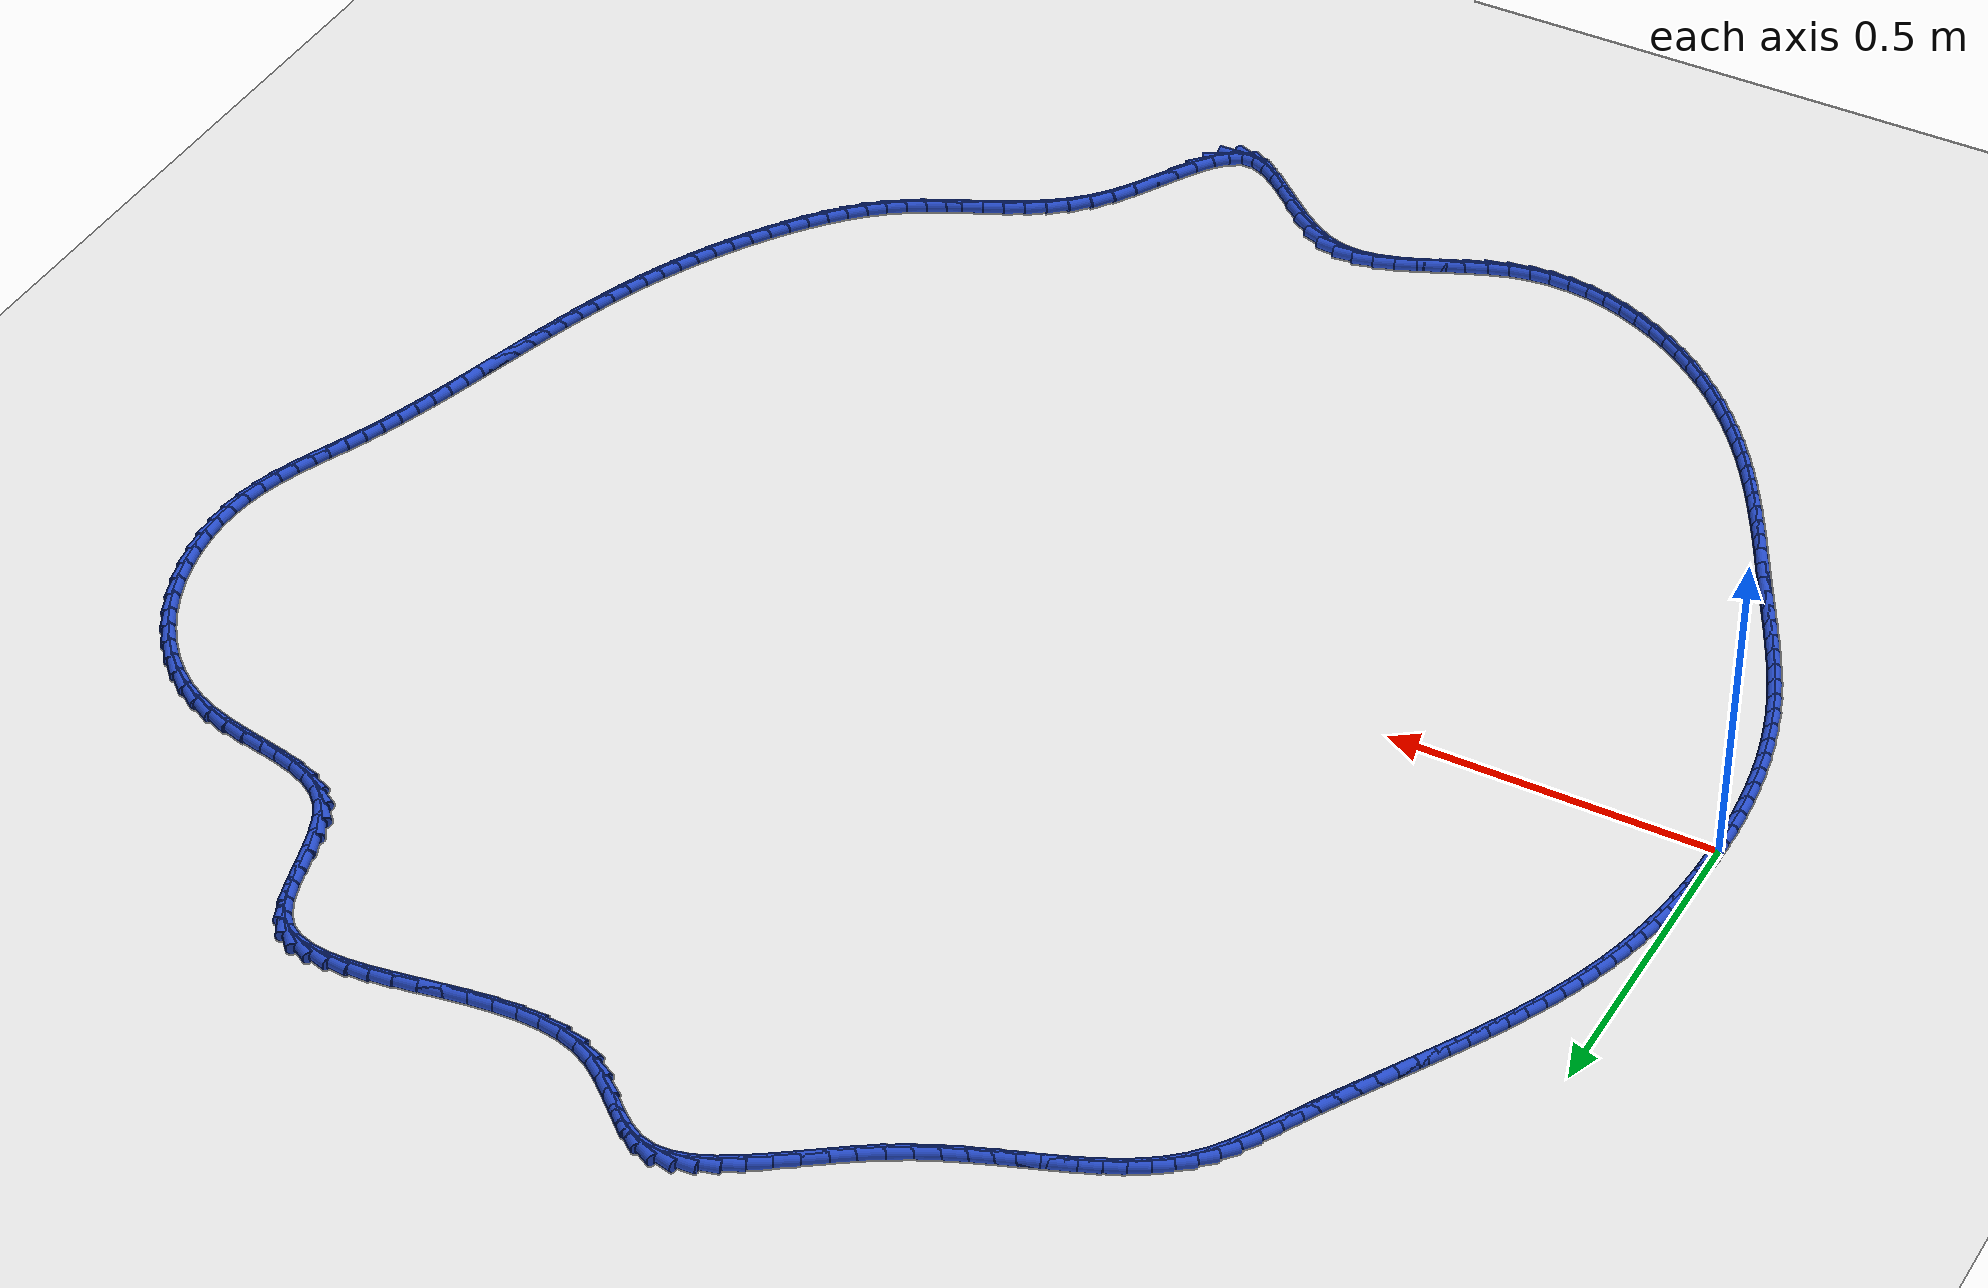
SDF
<sdf version="1.6">
 <world name="default">
  <light name="sun" type="directional">
   <pose>0 0 10 0 -0 0</pose>
   <diffuse>0.8 0.8 0.8 1</diffuse>
   <specular>0.2 0.2 0.2 1</specular>
   <attenuation>
    <range>1000</range>
    <constant>0.9</constant>
    <linear>0.01</linear>
    <quadratic>0.001</quadratic>
   </attenuation>
   <direction>-0.5 0.1 -0.9</direction>
  </light>
  <model name="ground_plane">
   <static>1</static>
   <link name="link">
    <collision name="collision">
     <geometry><plane><normal>0 0 1</normal><size>100 100</size></plane></geometry>
     <surface><friction><ode><mu>100</mu><mu2>50</mu2></ode></friction></surface>
    </collision>
    <visual name="visual">
     <cast_shadows>0</cast_shadows>
     <geometry><plane><normal>0 0 1</normal><size>100 100</size></plane></geometry>
     <material>
      <script><uri>file://media/materials/scripts/gazebo.material</uri><name>Gazebo/WhiteGlow</name></script>
     </material>
    </visual>
   </link>
  </model>
  <gravity>0 0 -9.8</gravity>
  <magnetic_field>6e-06 2.3e-05 -4.2e-05</magnetic_field>
  <atmosphere type="adiabatic"/>
  <physics name="default_physics" default="0" type="ode">
   <max_step_size>0.001</max_step_size>
   <real_time_factor>1</real_time_factor>
   <real_time_update_rate>1000</real_time_update_rate>
  </physics>
  <scene><ambient>0.4 0.4 0.4 1</ambient><background>0.7 0.7 0.7 1</background><shadows>1</shadows></scene>
  <spherical_coordinates>
   <surface_model>EARTH_WGS84</surface_model>
   <latitude_deg>0</latitude_deg>
   <longitude_deg>0</longitude_deg>
   <elevation>0</elevation>
   <heading_deg>0</heading_deg>
  </spherical_coordinates>
  <model name="line">
   <link name="link_0">
    <pose>-1.1275702593849246e-17 6.938893903907228e-18 0.01 0 1.57 1.5528776744222816</pose>
    <collision name="collision">
     <geometry><cylinder><radius>0.01</radius><length>0.08</length></cylinder></geometry>
    </collision>
    <visual name="visual">
     <material>
      <script><name>Gazebo/Blue</name><uri>file://media/materials/scripts/gazebo.material</uri></script>
     </material>
     <geometry><cylinder><radius>0.01</radius><length>0.08</length></cylinder></geometry>
    </visual>
   </link>
   <link name="link_1">
    <pose>0.0005847356808313511 0.03262930076394987 0.01 0 1.57 1.5231234248671703</pose>
    <collision name="collision">
     <geometry><cylinder><radius>0.01</radius><length>0.08</length></cylinder></geometry>
    </collision>
    <visual name="visual">
     <material>
      <script><name>Gazebo/Blue</name><uri>file://media/materials/scripts/gazebo.material</uri></script>
     </material>
     <geometry><cylinder><radius>0.01</radius><length>0.08</length></cylinder></geometry>
    </visual>
   </link>
   <link name="link_2">
    <pose>0.0021392181864448552 0.06521185054207165 0.01 0 1.57 1.4924975641499387</pose>
    <collision name="collision">
     <geometry><cylinder><radius>0.01</radius><length>0.08</length></cylinder></geometry>
    </collision>
    <visual name="visual">
     <material>
      <script><name>Gazebo/Blue</name><uri>file://media/materials/scripts/gazebo.material</uri></script>
     </material>
     <geometry><cylinder><radius>0.01</radius><length>0.08</length></cylinder></geometry>
    </visual>
   </link>
   <link name="link_3">
    <pose>0.004687408967978583 0.09768977447747727 0.01 0 1.57 1.4608954747923455</pose>
    <collision name="collision">
     <geometry><cylinder><radius>0.01</radius><length>0.08</length></cylinder></geometry>
    </collision>
    <visual name="visual">
     <material>
      <script><name>Gazebo/Blue</name><uri>file://media/materials/scripts/gazebo.material</uri></script>
     </material>
     <geometry><cylinder><radius>0.01</radius><length>0.08</length></cylinder></geometry>
    </visual>
   </link>
   <link name="link_4">
    <pose>0.008253269476570608 0.1300051977132785 0.01 0 1.57 1.428212779567015</pose>
    <collision name="collision">
     <geometry><cylinder><radius>0.01</radius><length>0.08</length></cylinder></geometry>
    </collision>
    <visual name="visual">
     <material>
      <script><name>Gazebo/Blue</name><uri>file://media/materials/scripts/gazebo.material</uri></script>
     </material>
     <geometry><cylinder><radius>0.01</radius><length>0.08</length></cylinder></geometry>
    </visual>
   </link>
   <link name="link_5">
    <pose>0.012860761163359007 0.1621002453925873 0.01 0 1.57 1.3943459740241426</pose>
    <collision name="collision">
     <geometry><cylinder><radius>0.01</radius><length>0.08</length></cylinder></geometry>
    </collision>
    <visual name="visual">
     <material>
      <script><name>Gazebo/Blue</name><uri>file://media/materials/scripts/gazebo.material</uri></script>
     </material>
     <geometry><cylinder><radius>0.01</radius><length>0.08</length></cylinder></geometry>
    </visual>
   </link>
   <link name="link_6">
    <pose>0.01853384547948185 0.1939170426585154 0.01 0 1.57 1.359193421516529</pose>
    <collision name="collision">
     <geometry><cylinder><radius>0.01</radius><length>0.08</length></cylinder></geometry>
    </collision>
    <visual name="visual">
     <material>
      <script><name>Gazebo/Blue</name><uri>file://media/materials/scripts/gazebo.material</uri></script>
     </material>
     <geometry><cylinder><radius>0.01</radius><length>0.08</length></cylinder></geometry>
    </visual>
   </link>
   <link name="link_7">
    <pose>0.02529648387607722 0.22539771465417469 0.01 0 1.57 1.322656769166291</pose>
    <collision name="collision">
     <geometry><cylinder><radius>0.01</radius><length>0.08</length></cylinder></geometry>
    </collision>
    <visual name="visual">
     <material>
      <script><name>Gazebo/Blue</name><uri>file://media/materials/scripts/gazebo.material</uri></script>
     </material>
     <geometry><cylinder><radius>0.01</radius><length>0.08</length></cylinder></geometry>
    </visual>
   </link>
   <link name="link_8">
    <pose>0.03317263780428319 0.256484386522677 0.01 0 1.57 1.2846470649076709</pose>
    <collision name="collision">
     <geometry><cylinder><radius>0.01</radius><length>0.08</length></cylinder></geometry>
    </collision>
    <visual name="visual">
     <material>
      <script><name>Gazebo/Blue</name><uri>file://media/materials/scripts/gazebo.material</uri></script>
     </material>
     <geometry><cylinder><radius>0.01</radius><length>0.08</length></cylinder></geometry>
    </visual>
   </link>
   <link name="link_9">
    <pose>0.04218615847200757 0.2871192862710466 0.01 0 1.57 1.2463314492588073</pose>
    <collision name="collision">
     <geometry><cylinder><radius>0.01</radius><length>0.08</length></cylinder></geometry>
    </collision>
    <visual name="visual">
     <material>
      <script><name>Gazebo/Blue</name><uri>file://media/materials/scripts/gazebo.material</uri></script>
     </material>
     <geometry><cylinder><radius>0.01</radius><length>0.08</length></cylinder></geometry>
    </visual>
   </link>
   <link name="link_10">
    <pose>0.05232891794545917 0.3172744804698456 0.01 0 1.57 1.2107497144841182</pose>
    <collision name="collision">
     <geometry><cylinder><radius>0.01</radius><length>0.08</length></cylinder></geometry>
    </collision>
    <visual name="visual">
     <material>
      <script><name>Gazebo/Blue</name><uri>file://media/materials/scripts/gazebo.material</uri></script>
     </material>
     <geometry><cylinder><radius>0.01</radius><length>0.08</length></cylinder></geometry>
    </visual>
   </link>
   <link name="link_11">
    <pose>0.06351666048580978 0.3469930677507514 0.01 0 1.57 1.1784972051245906</pose>
    <collision name="collision">
     <geometry><cylinder><radius>0.01</radius><length>0.08</length></cylinder></geometry>
    </collision>
    <visual name="visual">
     <material>
      <script><name>Gazebo/Blue</name><uri>file://media/materials/scripts/gazebo.material</uri></script>
     </material>
     <geometry><cylinder><radius>0.01</radius><length>0.08</length></cylinder></geometry>
    </visual>
   </link>
   <link name="link_12">
    <pose>0.07565404607466868 0.37632848907992666 0.01 0 1.57 1.1496890651347498</pose>
    <collision name="collision">
     <geometry><cylinder><radius>0.01</radius><length>0.08</length></cylinder></geometry>
    </collision>
    <visual name="visual">
     <material>
      <script><name>Gazebo/Blue</name><uri>file://media/materials/scripts/gazebo.material</uri></script>
     </material>
     <geometry><cylinder><radius>0.01</radius><length>0.08</length></cylinder></geometry>
    </visual>
   </link>
   <link name="link_13">
    <pose>0.08864573469364508 0.405334185423534 0.01 0 1.57 1.1243934355770457</pose>
    <collision name="collision">
     <geometry><cylinder><radius>0.01</radius><length>0.08</length></cylinder></geometry>
    </collision>
    <visual name="visual">
     <material>
      <script><name>Gazebo/Blue</name><uri>file://media/materials/scripts/gazebo.material</uri></script>
     </material>
     <geometry><cylinder><radius>0.01</radius><length>0.08</length></cylinder></geometry>
    </visual>
   </link>
   <link name="link_14">
    <pose>0.10239638632434825 0.4340635977477362 0.01 0 1.57 1.1026409555502208</pose>
    <collision name="collision">
     <geometry><cylinder><radius>0.01</radius><length>0.08</length></cylinder></geometry>
    </collision>
    <visual name="visual">
     <material>
      <script><name>Gazebo/Blue</name><uri>file://media/materials/scripts/gazebo.material</uri></script>
     </material>
     <geometry><cylinder><radius>0.01</radius><length>0.08</length></cylinder></geometry>
    </visual>
   </link>
   <link name="link_15">
    <pose>0.11681066094838743 0.46257016701869563 0.01 0 1.57 1.0844339729226653</pose>
    <collision name="collision">
     <geometry><cylinder><radius>0.01</radius><length>0.08</length></cylinder></geometry>
    </collision>
    <visual name="visual">
     <material>
      <script><name>Gazebo/Blue</name><uri>file://media/materials/scripts/gazebo.material</uri></script>
     </material>
     <geometry><cylinder><radius>0.01</radius><length>0.08</length></cylinder></geometry>
    </visual>
   </link>
   <link name="link_16">
    <pose>0.13179321854737192 0.4909073342025754 0.01 0 1.57 1.0697548475673473</pose>
    <collision name="collision">
     <geometry><cylinder><radius>0.01</radius><length>0.08</length></cylinder></geometry>
    </collision>
    <visual name="visual">
     <material>
      <script><name>Gazebo/Blue</name><uri>file://media/materials/scripts/gazebo.material</uri></script>
     </material>
     <geometry><cylinder><radius>0.01</radius><length>0.08</length></cylinder></geometry>
    </visual>
   </link>
   <link name="link_17">
    <pose>0.14724871910291085 0.5191285402655377 0.01 0 1.57 1.0585729898277936</pose>
    <collision name="collision">
     <geometry><cylinder><radius>0.01</radius><length>0.08</length></cylinder></geometry>
    </collision>
    <visual name="visual">
     <material>
      <script><name>Gazebo/Blue</name><uri>file://media/materials/scripts/gazebo.material</uri></script>
     </material>
     <geometry><cylinder><radius>0.01</radius><length>0.08</length></cylinder></geometry>
    </visual>
   </link>
   <link name="link_18">
    <pose>0.16308182259661358 0.5472872261737454 0.01 0 1.57 1.0508504763976023</pose>
    <collision name="collision">
     <geometry><cylinder><radius>0.01</radius><length>0.08</length></cylinder></geometry>
    </collision>
    <visual name="visual">
     <material>
      <script><name>Gazebo/Blue</name><uri>file://media/materials/scripts/gazebo.material</uri></script>
     </material>
     <geometry><cylinder><radius>0.01</radius><length>0.08</length></cylinder></geometry>
    </visual>
   </link>
   <link name="link_19">
    <pose>0.17919718901008924 0.5754368328933609 0.01 0 1.57 1.0465462204213678</pose>
    <collision name="collision">
     <geometry><cylinder><radius>0.01</radius><length>0.08</length></cylinder></geometry>
    </collision>
    <visual name="visual">
     <material>
      <script><name>Gazebo/Blue</name><uri>file://media/materials/scripts/gazebo.material</uri></script>
     </material>
     <geometry><cylinder><radius>0.01</radius><length>0.08</length></cylinder></geometry>
    </visual>
   </link>
   <link name="link_20">
    <pose>0.19549947832494713 0.6036308013905471 0.01 0 1.57 1.045618751043367</pose>
    <collision name="collision">
     <geometry><cylinder><radius>0.01</radius><length>0.08</length></cylinder></geometry>
    </collision>
    <visual name="visual">
     <material>
      <script><name>Gazebo/Blue</name><uri>file://media/materials/scripts/gazebo.material</uri></script>
     </material>
     <geometry><cylinder><radius>0.01</radius><length>0.08</length></cylinder></geometry>
    </visual>
   </link>
   <link name="link_21">
    <pose>0.21189335052279656 0.6319225726314667 0.01 0 1.57 1.048027693953845</pose>
    <collision name="collision">
     <geometry><cylinder><radius>0.01</radius><length>0.08</length></cylinder></geometry>
    </collision>
    <visual name="visual">
     <material>
      <script><name>Gazebo/Blue</name><uri>file://media/materials/scripts/gazebo.material</uri></script>
     </material>
     <geometry><cylinder><radius>0.01</radius><length>0.08</length></cylinder></geometry>
    </visual>
   </link>
   <link name="link_22">
    <pose>0.22828346558524665 0.660365587582282 0.01 0 1.57 1.053734053638647</pose>
    <collision name="collision">
     <geometry><cylinder><radius>0.01</radius><length>0.08</length></cylinder></geometry>
    </collision>
    <visual name="visual">
     <material>
      <script><name>Gazebo/Blue</name><uri>file://media/materials/scripts/gazebo.material</uri></script>
     </material>
     <geometry><cylinder><radius>0.01</radius><length>0.08</length></cylinder></geometry>
    </visual>
   </link>
   <link name="link_23">
    <pose>0.2445744834939068 0.6890132872091559 0.01 0 1.57 1.0626993934705855</pose>
    <collision name="collision">
     <geometry><cylinder><radius>0.01</radius><length>0.08</length></cylinder></geometry>
    </collision>
    <visual name="visual">
     <material>
      <script><name>Gazebo/Blue</name><uri>file://media/materials/scripts/gazebo.material</uri></script>
     </material>
     <geometry><cylinder><radius>0.01</radius><length>0.08</length></cylinder></geometry>
    </visual>
   </link>
   <link name="link_24">
    <pose>0.26067106423038616 0.7179191124782511 0.01 0 1.57 1.0748840027256776</pose>
    <collision name="collision">
     <geometry><cylinder><radius>0.01</radius><length>0.08</length></cylinder></geometry>
    </collision>
    <visual name="visual">
     <material>
      <script><name>Gazebo/Blue</name><uri>file://media/materials/scripts/gazebo.material</uri></script>
     </material>
     <geometry><cylinder><radius>0.01</radius><length>0.08</length></cylinder></geometry>
    </visual>
   </link>
   <link name="link_25">
    <pose>0.2764778677762939 0.7471365043557301 0.01 0 1.57 1.0858496951649557</pose>
    <collision name="collision">
     <geometry><cylinder><radius>0.01</radius><length>0.08</length></cylinder></geometry>
    </collision>
    <visual name="visual">
     <material>
      <script><name>Gazebo/Blue</name><uri>file://media/materials/scripts/gazebo.material</uri></script>
     </material>
     <geometry><cylinder><radius>0.01</radius><length>0.08</length></cylinder></geometry>
    </visual>
   </link>
   <link name="link_26">
    <pose>0.2919996080275518 0.7765943025526106 0.01 0 1.57 1.0745052722925703</pose>
    <collision name="collision">
     <geometry><cylinder><radius>0.01</radius><length>0.08</length></cylinder></geometry>
    </collision>
    <visual name="visual">
     <material>
      <script><name>Gazebo/Blue</name><uri>file://media/materials/scripts/gazebo.material</uri></script>
     </material>
     <geometry><cylinder><radius>0.01</radius><length>0.08</length></cylinder></geometry>
    </visual>
   </link>
   <link name="link_27">
    <pose>0.30771971972837653 0.805625176015661 0.01 0 1.57 1.033300610092213</pose>
    <collision name="collision">
     <geometry><cylinder><radius>0.01</radius><length>0.08</length></cylinder></geometry>
    </collision>
    <visual name="visual">
     <material>
      <script><name>Gazebo/Blue</name><uri>file://media/materials/scripts/gazebo.material</uri></script>
     </material>
     <geometry><cylinder><radius>0.01</radius><length>0.08</length></cylinder></geometry>
    </visual>
   </link>
   <link name="link_28">
    <pose>0.3242646478944526 0.8333836971179575 0.01 0 1.57 0.9588224311259876</pose>
    <collision name="collision">
     <geometry><cylinder><radius>0.01</radius><length>0.08</length></cylinder></geometry>
    </collision>
    <visual name="visual">
     <material>
      <script><name>Gazebo/Blue</name><uri>file://media/materials/scripts/gazebo.material</uri></script>
     </material>
     <geometry><cylinder><radius>0.01</radius><length>0.08</length></cylinder></geometry>
    </visual>
   </link>
   <link name="link_29">
    <pose>0.3422608629879262 0.8590244065430506 0.01 0 1.57 0.8484412714449183</pose>
    <collision name="collision">
     <geometry><cylinder><radius>0.01</radius><length>0.08</length></cylinder></geometry>
    </collision>
    <visual name="visual">
     <material>
      <script><name>Gazebo/Blue</name><uri>file://media/materials/scripts/gazebo.material</uri></script>
     </material>
     <geometry><cylinder><radius>0.01</radius><length>0.08</length></cylinder></geometry>
    </visual>
   </link>
   <link name="link_30">
    <pose>0.36229711500374795 0.8817607542497047 0.01 0 1.57 0.7280725384580512</pose>
    <collision name="collision">
     <geometry><cylinder><radius>0.01</radius><length>0.08</length></cylinder></geometry>
    </collision>
    <visual name="visual">
     <material>
      <script><name>Gazebo/Blue</name><uri>file://media/materials/scripts/gazebo.material</uri></script>
     </material>
     <geometry><cylinder><radius>0.01</radius><length>0.08</length></cylinder></geometry>
    </visual>
   </link>
   <link name="link_31">
    <pose>0.38448955726475376 0.9015442597247725 0.01 0 1.57 0.6213461389352507</pose>
    <collision name="collision">
     <geometry><cylinder><radius>0.01</radius><length>0.08</length></cylinder></geometry>
    </collision>
    <visual name="visual">
     <material>
      <script><name>Gazebo/Blue</name><uri>file://media/materials/scripts/gazebo.material</uri></script>
     </material>
     <geometry><cylinder><radius>0.01</radius><length>0.08</length></cylinder></geometry>
    </visual>
   </link>
   <link name="link_32">
    <pose>0.4086324298595755 0.9188291847782641 0.01 0 1.57 0.5324682248640784</pose>
    <collision name="collision">
     <geometry><cylinder><radius>0.01</radius><length>0.08</length></cylinder></geometry>
    </collision>
    <visual name="visual">
     <material>
      <script><name>Gazebo/Blue</name><uri>file://media/materials/scripts/gazebo.material</uri></script>
     </material>
     <geometry><cylinder><radius>0.01</radius><length>0.08</length></cylinder></geometry>
    </visual>
   </link>
   <link name="link_33">
    <pose>0.4345137888299921 0.9340794490464314 0.01 0 1.57 0.4629343465894515</pose>
    <collision name="collision">
     <geometry><cylinder><radius>0.01</radius><length>0.08</length></cylinder></geometry>
    </collision>
    <visual name="visual">
     <material>
      <script><name>Gazebo/Blue</name><uri>file://media/materials/scripts/gazebo.material</uri></script>
     </material>
     <geometry><cylinder><radius>0.01</radius><length>0.08</length></cylinder></geometry>
    </visual>
   </link>
   <link name="link_34">
    <pose>0.46192169021778257 0.9477589721655271 0.01 0 1.57 0.41260352555230706</pose>
    <collision name="collision">
     <geometry><cylinder><radius>0.01</radius><length>0.08</length></cylinder></geometry>
    </collision>
    <visual name="visual">
     <material>
      <script><name>Gazebo/Blue</name><uri>file://media/materials/scripts/gazebo.material</uri></script>
     </material>
     <geometry><cylinder><radius>0.01</radius><length>0.08</length></cylinder></geometry>
    </visual>
   </link>
   <link name="link_35">
    <pose>0.49064419006472604 0.9603316737718033 0.01 0 1.57 0.380498803944782</pose>
    <collision name="collision">
     <geometry><cylinder><radius>0.01</radius><length>0.08</length></cylinder></geometry>
    </collision>
    <visual name="visual">
     <material>
      <script><name>Gazebo/Blue</name><uri>file://media/materials/scripts/gazebo.material</uri></script>
     </material>
     <geometry><cylinder><radius>0.01</radius><length>0.08</length></cylinder></geometry>
    </visual>
   </link>
   <link name="link_36">
    <pose>0.5204693444126015 0.9722614735015124 0.01 0 1.57 0.3653865229257871</pose>
    <collision name="collision">
     <geometry><cylinder><radius>0.01</radius><length>0.08</length></cylinder></geometry>
    </collision>
    <visual name="visual">
     <material>
      <script><name>Gazebo/Blue</name><uri>file://media/materials/scripts/gazebo.material</uri></script>
     </material>
     <geometry><cylinder><radius>0.01</radius><length>0.08</length></cylinder></geometry>
    </visual>
   </link>
   <link name="link_37">
    <pose>0.551185209303188 0.984012290990907 0.01 0 1.57 0.3660883460650384</pose>
    <collision name="collision">
     <geometry><cylinder><radius>0.01</radius><length>0.08</length></cylinder></geometry>
    </collision>
    <visual name="visual">
     <material>
      <script><name>Gazebo/Blue</name><uri>file://media/materials/scripts/gazebo.material</uri></script>
     </material>
     <geometry><cylinder><radius>0.01</radius><length>0.08</length></cylinder></geometry>
    </visual>
   </link>
   <link name="link_38">
    <pose>0.5825798407782645 0.9960480458762393 0.01 0 1.57 0.3815889988238801</pose>
    <collision name="collision">
     <geometry><cylinder><radius>0.01</radius><length>0.08</length></cylinder></geometry>
    </collision>
    <visual name="visual">
     <material>
      <script><name>Gazebo/Blue</name><uri>file://media/materials/scripts/gazebo.material</uri></script>
     </material>
     <geometry><cylinder><radius>0.01</radius><length>0.08</length></cylinder></geometry>
    </visual>
   </link>
   <link name="link_39">
    <pose>0.6144412948796102 1.0088326577937616 0.01 0 1.57 0.4110112078242422</pose>
    <collision name="collision">
     <geometry><cylinder><radius>0.01</radius><length>0.08</length></cylinder></geometry>
    </collision>
    <visual name="visual">
     <material>
      <script><name>Gazebo/Blue</name><uri>file://media/materials/scripts/gazebo.material</uri></script>
     </material>
     <geometry><cylinder><radius>0.01</radius><length>0.08</length></cylinder></geometry>
    </visual>
   </link>
   <link name="link_40">
    <pose>0.6465576276490039 1.0228300463797264 0.01 0 1.57 0.45350829984810603</pose>
    <collision name="collision">
     <geometry><cylinder><radius>0.01</radius><length>0.08</length></cylinder></geometry>
    </collision>
    <visual name="visual">
     <material>
      <script><name>Gazebo/Blue</name><uri>file://media/materials/scripts/gazebo.material</uri></script>
     </material>
     <geometry><cylinder><radius>0.01</radius><length>0.08</length></cylinder></geometry>
    </visual>
   </link>
   <link name="link_41">
    <pose>0.6787168951282248 1.0385041312703864 0.01 0 1.57 0.508109195391346</pose>
    <collision name="collision">
     <geometry><cylinder><radius>0.01</radius><length>0.08</length></cylinder></geometry>
    </collision>
    <visual name="visual">
     <material>
      <script><name>Gazebo/Blue</name><uri>file://media/materials/scripts/gazebo.material</uri></script>
     </material>
     <geometry><cylinder><radius>0.01</radius><length>0.08</length></cylinder></geometry>
    </visual>
   </link>
   <link name="link_42">
    <pose>0.7107071533592332 1.0563188321001777 0.01 0 1.57 0.567286772332727</pose>
    <collision name="collision">
     <geometry><cylinder><radius>0.01</radius><length>0.08</length></cylinder></geometry>
    </collision>
    <visual name="visual">
     <material>
      <script><name>Gazebo/Blue</name><uri>file://media/materials/scripts/gazebo.material</uri></script>
     </material>
     <geometry><cylinder><radius>0.01</radius><length>0.08</length></cylinder></geometry>
    </visual>
   </link>
   <link name="link_43">
    <pose>0.7423427171915445 1.076475344786256 0.01 0 1.57 0.6067329364674294</pose>
    <collision name="collision">
     <geometry><cylinder><radius>0.01</radius><length>0.08</length></cylinder></geometry>
    </collision>
    <visual name="visual">
     <material>
      <script><name>Gazebo/Blue</name><uri>file://media/materials/scripts/gazebo.material</uri></script>
     </material>
     <geometry><cylinder><radius>0.01</radius><length>0.08</length></cylinder></geometry>
    </visual>
   </link>
   <link name="link_44">
    <pose>0.7735423371002607 1.0981299695202624 0.01 0 1.57 0.6227193008463253</pose>
    <collision name="collision">
     <geometry><cylinder><radius>0.01</radius><length>0.08</length></cylinder></geometry>
    </collision>
    <visual name="visual">
     <material>
      <script><name>Gazebo/Blue</name><uri>file://media/materials/scripts/gazebo.material</uri></script>
     </material>
     <geometry><cylinder><radius>0.01</radius><length>0.08</length></cylinder></geometry>
    </visual>
   </link>
   <link name="link_45">
    <pose>0.804250723420461 1.1201792737965626 0.01 0 1.57 0.6157646337579946</pose>
    <collision name="collision">
     <geometry><cylinder><radius>0.01</radius><length>0.08</length></cylinder></geometry>
    </collision>
    <visual name="visual">
     <material>
      <script><name>Gazebo/Blue</name><uri>file://media/materials/scripts/gazebo.material</uri></script>
     </material>
     <geometry><cylinder><radius>0.01</radius><length>0.08</length></cylinder></geometry>
    </visual>
   </link>
   <link name="link_46">
    <pose>0.834412586487225 1.1415198251095215 0.01 0 1.57 0.5838143093946124</pose>
    <collision name="collision">
     <geometry><cylinder><radius>0.01</radius><length>0.08</length></cylinder></geometry>
    </collision>
    <visual name="visual">
     <material>
      <script><name>Gazebo/Blue</name><uri>file://media/materials/scripts/gazebo.material</uri></script>
     </material>
     <geometry><cylinder><radius>0.01</radius><length>0.08</length></cylinder></geometry>
    </visual>
   </link>
   <link name="link_47">
    <pose>0.8639726366356327 1.1610481909535053 0.01 0 1.57 0.5216666310306911</pose>
    <collision name="collision">
     <geometry><cylinder><radius>0.01</radius><length>0.08</length></cylinder></geometry>
    </collision>
    <visual name="visual">
     <material>
      <script><name>Gazebo/Blue</name><uri>file://media/materials/scripts/gazebo.material</uri></script>
     </material>
     <geometry><cylinder><radius>0.01</radius><length>0.08</length></cylinder></geometry>
    </visual>
   </link>
   <link name="link_48">
    <pose>0.8928755842007632 1.1776609388228794 0.01 0 1.57 0.4201351287948398</pose>
    <collision name="collision">
     <geometry><cylinder><radius>0.01</radius><length>0.08</length></cylinder></geometry>
    </collision>
    <visual name="visual">
     <material>
      <script><name>Gazebo/Blue</name><uri>file://media/materials/scripts/gazebo.material</uri></script>
     </material>
     <geometry><cylinder><radius>0.01</radius><length>0.08</length></cylinder></geometry>
    </visual>
   </link>
   <link name="link_49">
    <pose>0.9210661395176958 1.1902546362120083 0.01 0 1.57 0.2659889485143995</pose>
    <collision name="collision">
     <geometry><cylinder><radius>0.01</radius><length>0.08</length></cylinder></geometry>
    </collision>
    <visual name="visual">
     <material>
      <script><name>Gazebo/Blue</name><uri>file://media/materials/scripts/gazebo.material</uri></script>
     </material>
     <geometry><cylinder><radius>0.01</radius><length>0.08</length></cylinder></geometry>
    </visual>
   </link>
   <link name="link_50">
    <pose>0.94848901292151 1.1977258506152586 0.01 0 1.57 0.046781763627913406</pose>
    <collision name="collision">
     <geometry><cylinder><radius>0.01</radius><length>0.08</length></cylinder></geometry>
    </collision>
    <visual name="visual">
     <material>
      <script><name>Gazebo/Blue</name><uri>file://media/materials/scripts/gazebo.material</uri></script>
     </material>
     <geometry><cylinder><radius>0.01</radius><length>0.08</length></cylinder></geometry>
    </visual>
   </link>
   <link name="link_51">
    <pose>0.975088914747286 1.1989711495269955 0.01 0 1.57 -0.2321958898249655</pose>
    <collision name="collision">
     <geometry><cylinder><radius>0.01</radius><length>0.08</length></cylinder></geometry>
    </collision>
    <visual name="visual">
     <material>
      <script><name>Gazebo/Blue</name><uri>file://media/materials/scripts/gazebo.material</uri></script>
     </material>
     <geometry><cylinder><radius>0.01</radius><length>0.08</length></cylinder></geometry>
    </visual>
   </link>
   <link name="link_52">
    <pose>1.0008108881434359 1.1928889102725122 0.01 0 1.57 -0.4996764793595446</pose>
    <collision name="collision">
     <geometry><cylinder><radius>0.01</radius><length>0.08</length></cylinder></geometry>
    </collision>
    <visual name="visual">
     <material>
      <script><name>Gazebo/Blue</name><uri>file://media/materials/scripts/gazebo.material</uri></script>
     </material>
     <geometry><cylinder><radius>0.01</radius><length>0.08</length></cylinder></geometry>
    </visual>
   </link>
   <link name="link_53">
    <pose>1.025763661771811 1.1792676280756986 0.01 0 1.57 -0.6565288735923052</pose>
    <collision name="collision">
     <geometry><cylinder><radius>0.01</radius><length>0.08</length></cylinder></geometry>
    </collision>
    <visual name="visual">
     <material>
      <script><name>Gazebo/Blue</name><uri>file://media/materials/scripts/gazebo.material</uri></script>
     </material>
     <geometry><cylinder><radius>0.01</radius><length>0.08</length></cylinder></geometry>
    </visual>
   </link>
   <link name="link_54">
    <pose>1.0504833121993074 1.1602197058246835 0.01 0 1.57 -0.7195655072326672</pose>
    <collision name="collision">
     <geometry><cylinder><radius>0.01</radius><length>0.08</length></cylinder></geometry>
    </collision>
    <visual name="visual">
     <material>
      <script><name>Gazebo/Blue</name><uri>file://media/materials/scripts/gazebo.material</uri></script>
     </material>
     <geometry><cylinder><radius>0.01</radius><length>0.08</length></cylinder></geometry>
    </visual>
   </link>
   <link name="link_55">
    <pose>1.0755747861341562 1.1382320605853902 0.01 0 1.57 -0.7107506771846369</pose>
    <collision name="collision">
     <geometry><cylinder><radius>0.01</radius><length>0.08</length></cylinder></geometry>
    </collision>
    <visual name="visual">
     <material>
      <script><name>Gazebo/Blue</name><uri>file://media/materials/scripts/gazebo.material</uri></script>
     </material>
     <geometry><cylinder><radius>0.01</radius><length>0.08</length></cylinder></geometry>
    </visual>
   </link>
   <link name="link_56">
    <pose>1.101643030284589 1.115791609423741 0.01 0 1.57 -0.6357924272160159</pose>
    <collision name="collision">
     <geometry><cylinder><radius>0.01</radius><length>0.08</length></cylinder></geometry>
    </collision>
    <visual name="visual">
     <material>
      <script><name>Gazebo/Blue</name><uri>file://media/materials/scripts/gazebo.material</uri></script>
     </material>
     <geometry><cylinder><radius>0.01</radius><length>0.08</length></cylinder></geometry>
    </visual>
   </link>
   <link name="link_57">
    <pose>1.1292929913588372 1.0953852694056572 0.01 0 1.57 -0.4900527705464352</pose>
    <collision name="collision">
     <geometry><cylinder><radius>0.01</radius><length>0.08</length></cylinder></geometry>
    </collision>
    <visual name="visual">
     <material>
      <script><name>Gazebo/Blue</name><uri>file://media/materials/scripts/gazebo.material</uri></script>
     </material>
     <geometry><cylinder><radius>0.01</radius><length>0.08</length></cylinder></geometry>
    </visual>
   </link>
   <link name="link_58">
    <pose>1.1591211371965457 1.0794732680540715 0.01 0 1.57 -0.30864110166584946</pose>
    <collision name="collision">
     <geometry><cylinder><radius>0.01</radius><length>0.08</length></cylinder></geometry>
    </collision>
    <visual name="visual">
     <material>
      <script><name>Gazebo/Blue</name><uri>file://media/materials/scripts/gazebo.material</uri></script>
     </material>
     <geometry><cylinder><radius>0.01</radius><length>0.08</length></cylinder></geometry>
    </visual>
   </link>
   <link name="link_59">
    <pose>1.1913093194147997 1.0692107156601955 0.01 0 1.57 -0.15479637146300426</pose>
    <collision name="collision">
     <geometry><cylinder><radius>0.01</radius><length>0.08</length></cylinder></geometry>
    </collision>
    <visual name="visual">
     <material>
      <script><name>Gazebo/Blue</name><uri>file://media/materials/scripts/gazebo.material</uri></script>
     </material>
     <geometry><cylinder><radius>0.01</radius><length>0.08</length></cylinder></geometry>
    </visual>
   </link>
   <link name="link_60">
    <pose>1.2254456969182623 1.0638839133679794 0.01 0 1.57 -0.03503644360958951</pose>
    <collision name="collision">
     <geometry><cylinder><radius>0.01</radius><length>0.08</length></cylinder></geometry>
    </collision>
    <visual name="visual">
     <material>
      <script><name>Gazebo/Blue</name><uri>file://media/materials/scripts/gazebo.material</uri></script>
     </material>
     <geometry><cylinder><radius>0.01</radius><length>0.08</length></cylinder></geometry>
    </visual>
   </link>
   <link name="link_61">
    <pose>1.2610726810801538 1.0626351595343433 0.01 0 1.57 0.053728732022189224</pose>
    <collision name="collision">
     <geometry><cylinder><radius>0.01</radius><length>0.08</length></cylinder></geometry>
    </collision>
    <visual name="visual">
     <material>
      <script><name>Gazebo/Blue</name><uri>file://media/materials/scripts/gazebo.material</uri></script>
     </material>
     <geometry><cylinder><radius>0.01</radius><length>0.08</length></cylinder></geometry>
    </visual>
   </link>
   <link name="link_62">
    <pose>1.2977326832736926 1.064606752516207 0.01 0 1.57 0.11587943171663884</pose>
    <collision name="collision">
     <geometry><cylinder><radius>0.01</radius><length>0.08</length></cylinder></geometry>
    </collision>
    <visual name="visual">
     <material>
      <script><name>Gazebo/Blue</name><uri>file://media/materials/scripts/gazebo.material</uri></script>
     </material>
     <geometry><cylinder><radius>0.01</radius><length>0.08</length></cylinder></geometry>
    </visual>
   </link>
   <link name="link_63">
    <pose>1.3349681148720989 1.0689409906704912 0.01 0 1.57 0.15506816042027194</pose>
    <collision name="collision">
     <geometry><cylinder><radius>0.01</radius><length>0.08</length></cylinder></geometry>
    </collision>
    <visual name="visual">
     <material>
      <script><name>Gazebo/Blue</name><uri>file://media/materials/scripts/gazebo.material</uri></script>
     </material>
     <geometry><cylinder><radius>0.01</radius><length>0.08</length></cylinder></geometry>
    </visual>
   </link>
   <link name="link_64">
    <pose>1.3723213872485907 1.074780172354115 0.01 0 1.57 0.1734830740059691</pose>
    <collision name="collision">
     <geometry><cylinder><radius>0.01</radius><length>0.08</length></cylinder></geometry>
    </collision>
    <visual name="visual">
     <material>
      <script><name>Gazebo/Blue</name><uri>file://media/materials/scripts/gazebo.material</uri></script>
     </material>
     <geometry><cylinder><radius>0.01</radius><length>0.08</length></cylinder></geometry>
    </visual>
   </link>
   <link name="link_65">
    <pose>1.4093349117763887 1.0812665959239998 0.01 0 1.57 0.1715876228042831</pose>
    <collision name="collision">
     <geometry><cylinder><radius>0.01</radius><length>0.08</length></cylinder></geometry>
    </collision>
    <visual name="visual">
     <material>
      <script><name>Gazebo/Blue</name><uri>file://media/materials/scripts/gazebo.material</uri></script>
     </material>
     <geometry><cylinder><radius>0.01</radius><length>0.08</length></cylinder></geometry>
    </visual>
   </link>
   <link name="link_66">
    <pose>1.445551099828712 1.0875425597370647 0.01 0 1.57 0.1478719134858487</pose>
    <collision name="collision">
     <geometry><cylinder><radius>0.01</radius><length>0.08</length></cylinder></geometry>
    </collision>
    <visual name="visual">
     <material>
      <script><name>Gazebo/Blue</name><uri>file://media/materials/scripts/gazebo.material</uri></script>
     </material>
     <geometry><cylinder><radius>0.01</radius><length>0.08</length></cylinder></geometry>
    </visual>
   </link>
   <link name="link_67">
    <pose>1.48051236277878 1.0927503621502306 0.01 0 1.57 0.09838993190267431</pose>
    <collision name="collision">
     <geometry><cylinder><radius>0.01</radius><length>0.08</length></cylinder></geometry>
    </collision>
    <visual name="visual">
     <material>
      <script><name>Gazebo/Blue</name><uri>file://media/materials/scripts/gazebo.material</uri></script>
     </material>
     <geometry><cylinder><radius>0.01</radius><length>0.08</length></cylinder></geometry>
    </visual>
   </link>
   <link name="link_68">
    <pose>1.513761111999812 1.0960323015204174 0.01 0 1.57 0.016034545317960506</pose>
    <collision name="collision">
     <geometry><cylinder><radius>0.01</radius><length>0.08</length></cylinder></geometry>
    </collision>
    <visual name="visual">
     <material>
      <script><name>Gazebo/Blue</name><uri>file://media/materials/scripts/gazebo.material</uri></script>
     </material>
     <geometry><cylinder><radius>0.01</radius><length>0.08</length></cylinder></geometry>
    </visual>
   </link>
   <link name="link_69">
    <pose>1.5448397588650271 1.0965306762045448 0.01 0 1.57 -0.11002091675937706</pose>
    <collision name="collision">
     <geometry><cylinder><radius>0.01</radius><length>0.08</length></cylinder></geometry>
    </collision>
    <visual name="visual">
     <material>
      <script><name>Gazebo/Blue</name><uri>file://media/materials/scripts/gazebo.material</uri></script>
     </material>
     <geometry><cylinder><radius>0.01</radius><length>0.08</length></cylinder></geometry>
    </visual>
   </link>
   <link name="link_70">
    <pose>1.5732907147476451 1.0933877845595334 0.01 0 1.57 -0.2926194399520623</pose>
    <collision name="collision">
     <geometry><cylinder><radius>0.01</radius><length>0.08</length></cylinder></geometry>
    </collision>
    <visual name="visual">
     <material>
      <script><name>Gazebo/Blue</name><uri>file://media/materials/scripts/gazebo.material</uri></script>
     </material>
     <geometry><cylinder><radius>0.01</radius><length>0.08</length></cylinder></geometry>
    </visual>
   </link>
   <link name="link_71">
    <pose>1.5986563910208855 1.0857459249423036 0.01 0 1.57 -0.5372071749215995</pose>
    <collision name="collision">
     <geometry><cylinder><radius>0.01</radius><length>0.08</length></cylinder></geometry>
    </collision>
    <visual name="visual">
     <material>
      <script><name>Gazebo/Blue</name><uri>file://media/materials/scripts/gazebo.material</uri></script>
     </material>
     <geometry><cylinder><radius>0.01</radius><length>0.08</length></cylinder></geometry>
    </visual>
   </link>
   <link name="link_72">
    <pose>1.6204791990579672 1.0727473957097748 0.01 0 1.57 -0.8224400972214115</pose>
    <collision name="collision">
     <geometry><cylinder><radius>0.01</radius><length>0.08</length></cylinder></geometry>
    </collision>
    <visual name="visual">
     <material>
      <script><name>Gazebo/Blue</name><uri>file://media/materials/scripts/gazebo.material</uri></script>
     </material>
     <geometry><cylinder><radius>0.01</radius><length>0.08</length></cylinder></geometry>
    </visual>
   </link>
   <link name="link_73">
    <pose>1.6383087406810088 1.0535455107085474 0.01 0 1.57 -1.0672424212627662</pose>
    <collision name="collision">
     <geometry><cylinder><radius>0.01</radius><length>0.08</length></cylinder></geometry>
    </collision>
    <visual name="visual">
     <material>
      <script><name>Gazebo/Blue</name><uri>file://media/materials/scripts/gazebo.material</uri></script>
     </material>
     <geometry><cylinder><radius>0.01</radius><length>0.08</length></cylinder></geometry>
    </visual>
   </link>
   <link name="link_74">
    <pose>1.652278671227364 1.0281883311869247 0.01 0 1.57 -1.2111819096715102</pose>
    <collision name="collision">
     <geometry><cylinder><radius>0.01</radius><length>0.08</length></cylinder></geometry>
    </collision>
    <visual name="visual">
     <material>
      <script><name>Gazebo/Blue</name><uri>file://media/materials/scripts/gazebo.material</uri></script>
     </material>
     <geometry><cylinder><radius>0.01</radius><length>0.08</length></cylinder></geometry>
    </visual>
   </link>
   <link name="link_75">
    <pose>1.6635286808114067 0.9982651247711927 0.01 0 1.57 -1.2808809340595608</pose>
    <collision name="collision">
     <geometry><cylinder><radius>0.01</radius><length>0.08</length></cylinder></geometry>
    </collision>
    <visual name="visual">
     <material>
      <script><name>Gazebo/Blue</name><uri>file://media/materials/scripts/gazebo.material</uri></script>
     </material>
     <geometry><cylinder><radius>0.01</radius><length>0.08</length></cylinder></geometry>
    </visual>
   </link>
   <link name="link_76">
    <pose>1.6732979508051204 0.9655175758472576 0.01 0 1.57 -1.2962737377099787</pose>
    <collision name="collision">
     <geometry><cylinder><radius>0.01</radius><length>0.08</length></cylinder></geometry>
    </collision>
    <visual name="visual">
     <material>
      <script><name>Gazebo/Blue</name><uri>file://media/materials/scripts/gazebo.material</uri></script>
     </material>
     <geometry><cylinder><radius>0.01</radius><length>0.08</length></cylinder></geometry>
    </visual>
   </link>
   <link name="link_77">
    <pose>1.682825662580487 0.9316873688010251 0.01 0 1.57 -1.2635412335321563</pose>
    <collision name="collision">
     <geometry><cylinder><radius>0.01</radius><length>0.08</length></cylinder></geometry>
    </collision>
    <visual name="visual">
     <material>
      <script><name>Gazebo/Blue</name><uri>file://media/materials/scripts/gazebo.material</uri></script>
     </material>
     <geometry><cylinder><radius>0.01</radius><length>0.08</length></cylinder></geometry>
    </visual>
   </link>
   <link name="link_78">
    <pose>1.6933509975094878 0.8985161880183997 0.01 0 1.57 -1.1776370423078908</pose>
    <collision name="collision">
     <geometry><cylinder><radius>0.01</radius><length>0.08</length></cylinder></geometry>
    </collision>
    <visual name="visual">
     <material>
      <script><name>Gazebo/Blue</name><uri>file://media/materials/scripts/gazebo.material</uri></script>
     </material>
     <geometry><cylinder><radius>0.01</radius><length>0.08</length></cylinder></geometry>
    </visual>
   </link>
   <link name="link_79">
    <pose>1.7061131369641056 0.8677457178852884 0.01 0 1.57 -1.023193186918059</pose>
    <collision name="collision">
     <geometry><cylinder><radius>0.01</radius><length>0.08</length></cylinder></geometry>
    </collision>
    <visual name="visual">
     <material>
      <script><name>Gazebo/Blue</name><uri>file://media/materials/scripts/gazebo.material</uri></script>
     </material>
     <geometry><cylinder><radius>0.01</radius><length>0.08</length></cylinder></geometry>
    </visual>
   </link>
   <link name="link_80">
    <pose>1.7223512623163224 0.8411176427875953 0.01 0 1.57 -0.789614595394106</pose>
    <collision name="collision">
     <geometry><cylinder><radius>0.01</radius><length>0.08</length></cylinder></geometry>
    </collision>
    <visual name="visual">
     <material>
      <script><name>Gazebo/Blue</name><uri>file://media/materials/scripts/gazebo.material</uri></script>
     </material>
     <geometry><cylinder><radius>0.01</radius><length>0.08</length></cylinder></geometry>
    </visual>
   </link>
   <link name="link_81">
    <pose>1.743145431809231 0.8201473753428853 0.01 0 1.57 -0.5566601003847765</pose>
    <collision name="collision">
     <geometry><cylinder><radius>0.01</radius><length>0.08</length></cylinder></geometry>
    </collision>
    <visual name="visual">
     <material>
      <script><name>Gazebo/Blue</name><uri>file://media/materials/scripts/gazebo.material</uri></script>
     </material>
     <geometry><cylinder><radius>0.01</radius><length>0.08</length></cylinder></geometry>
    </visual>
   </link>
   <link name="link_82">
    <pose>1.76827908080252 0.8045065411922556 0.01 0 1.57 -0.38317019445696415</pose>
    <collision name="collision">
     <geometry><cylinder><radius>0.01</radius><length>0.08</length></cylinder></geometry>
    </collision>
    <visual name="visual">
     <material>
      <script><name>Gazebo/Blue</name><uri>file://media/materials/scripts/gazebo.material</uri></script>
     </material>
     <geometry><cylinder><radius>0.01</radius><length>0.08</length></cylinder></geometry>
    </visual>
   </link>
   <link name="link_83">
    <pose>1.7969037011812574 0.7929681476018859 0.01 0 1.57 -0.27049728993500377</pose>
    <collision name="collision">
     <geometry><cylinder><radius>0.01</radius><length>0.08</length></cylinder></geometry>
    </collision>
    <visual name="visual">
     <material>
      <script><name>Gazebo/Blue</name><uri>file://media/materials/scripts/gazebo.material</uri></script>
     </material>
     <geometry><cylinder><radius>0.01</radius><length>0.08</length></cylinder></geometry>
    </visual>
   </link>
   <link name="link_84">
    <pose>1.8281665382837275 0.7842991632836813 0.01 0 1.57 -0.2096703374839424</pose>
    <collision name="collision">
     <geometry><cylinder><radius>0.01</radius><length>0.08</length></cylinder></geometry>
    </collision>
    <visual name="visual">
     <material>
      <script><name>Gazebo/Blue</name><uri>file://media/materials/scripts/gazebo.material</uri></script>
     </material>
     <geometry><cylinder><radius>0.01</radius><length>0.08</length></cylinder></geometry>
    </visual>
   </link>
   <link name="link_85">
    <pose>1.861214837448216 0.7772665569495478 0.01 0 1.57 -0.1926672878413611</pose>
    <collision name="collision">
     <geometry><cylinder><radius>0.01</radius><length>0.08</length></cylinder></geometry>
    </collision>
    <visual name="visual">
     <material>
      <script><name>Gazebo/Blue</name><uri>file://media/materials/scripts/gazebo.material</uri></script>
     </material>
     <geometry><cylinder><radius>0.01</radius><length>0.08</length></cylinder></geometry>
    </visual>
   </link>
   <link name="link_86">
    <pose>1.8951958440130063 0.7706372973113904 0.01 0 1.57 -0.21558490034325437</pose>
    <collision name="collision">
     <geometry><cylinder><radius>0.01</radius><length>0.08</length></cylinder></geometry>
    </collision>
    <visual name="visual">
     <material>
      <script><name>Gazebo/Blue</name><uri>file://media/materials/scripts/gazebo.material</uri></script>
     </material>
     <geometry><cylinder><radius>0.01</radius><length>0.08</length></cylinder></geometry>
    </visual>
   </link>
   <link name="link_87">
    <pose>1.9292568033163848 0.7631783530811147 0.01 0 1.57 -0.27859842074691027</pose>
    <collision name="collision">
     <geometry><cylinder><radius>0.01</radius><length>0.08</length></cylinder></geometry>
    </collision>
    <visual name="visual">
     <material>
      <script><name>Gazebo/Blue</name><uri>file://media/materials/scripts/gazebo.material</uri></script>
     </material>
     <geometry><cylinder><radius>0.01</radius><length>0.08</length></cylinder></geometry>
    </visual>
   </link>
   <link name="link_88">
    <pose>1.9625449606966345 0.7536566929706261 0.01 0 1.57 -0.38331644213271615</pose>
    <collision name="collision">
     <geometry><cylinder><radius>0.01</radius><length>0.08</length></cylinder></geometry>
    </collision>
    <visual name="visual">
     <material>
      <script><name>Gazebo/Blue</name><uri>file://media/materials/scripts/gazebo.material</uri></script>
     </material>
     <geometry><cylinder><radius>0.01</radius><length>0.08</length></cylinder></geometry>
    </visual>
   </link>
   <link name="link_89">
    <pose>1.9942279810291224 0.7408800919865076 0.01 0 1.57 -0.5062118793524274</pose>
    <collision name="collision">
     <geometry><cylinder><radius>0.01</radius><length>0.08</length></cylinder></geometry>
    </collision>
    <visual name="visual">
     <material>
      <script><name>Gazebo/Blue</name><uri>file://media/materials/scripts/gazebo.material</uri></script>
     </material>
     <geometry><cylinder><radius>0.01</radius><length>0.08</length></cylinder></geometry>
    </visual>
   </link>
   <link name="link_90">
    <pose>2.0238692358673864 0.7244471032637235 0.01 0 1.57 -0.6230400196634134</pose>
    <collision name="collision">
     <geometry><cylinder><radius>0.01</radius><length>0.08</length></cylinder></geometry>
    </collision>
    <visual name="visual">
     <material>
      <script><name>Gazebo/Blue</name><uri>file://media/materials/scripts/gazebo.material</uri></script>
     </material>
     <geometry><cylinder><radius>0.01</radius><length>0.08</length></cylinder></geometry>
    </visual>
   </link>
   <link name="link_91">
    <pose>2.051390622294713 0.7046727554556632 0.01 0 1.57 -0.7322050636445726</pose>
    <collision name="collision">
     <geometry><cylinder><radius>0.01</radius><length>0.08</length></cylinder></geometry>
    </collision>
    <visual name="visual">
     <material>
      <script><name>Gazebo/Blue</name><uri>file://media/materials/scripts/gazebo.material</uri></script>
     </material>
     <geometry><cylinder><radius>0.01</radius><length>0.08</length></cylinder></geometry>
    </visual>
   </link>
   <link name="link_92">
    <pose>2.076726997997753 0.681897977616793 0.01 0 1.57 -0.833753511895729</pose>
    <collision name="collision">
     <geometry><cylinder><radius>0.01</radius><length>0.08</length></cylinder></geometry>
    </collision>
    <visual name="visual">
     <material>
      <script><name>Gazebo/Blue</name><uri>file://media/materials/scripts/gazebo.material</uri></script>
     </material>
     <geometry><cylinder><radius>0.01</radius><length>0.08</length></cylinder></geometry>
    </visual>
   </link>
   <link name="link_93">
    <pose>2.099813220663158 0.6564636988015781 0.01 0 1.57 -0.9283039802490364</pose>
    <collision name="collision">
     <geometry><cylinder><radius>0.01</radius><length>0.08</length></cylinder></geometry>
    </collision>
    <visual name="visual">
     <material>
      <script><name>Gazebo/Blue</name><uri>file://media/materials/scripts/gazebo.material</uri></script>
     </material>
     <geometry><cylinder><radius>0.01</radius><length>0.08</length></cylinder></geometry>
    </visual>
   </link>
   <link name="link_94">
    <pose>2.1205841479775804 0.6287108480644846 0.01 0 1.57 -1.0168318100427638</pose>
    <collision name="collision">
     <geometry><cylinder><radius>0.01</radius><length>0.08</length></cylinder></geometry>
    </collision>
    <visual name="visual">
     <material>
      <script><name>Gazebo/Blue</name><uri>file://media/materials/scripts/gazebo.material</uri></script>
     </material>
     <geometry><cylinder><radius>0.01</radius><length>0.08</length></cylinder></geometry>
    </visual>
   </link>
   <link name="link_95">
    <pose>2.1389746376276713 0.598980354459978 0.01 0 1.57 -1.1005065122981406</pose>
    <collision name="collision">
     <geometry><cylinder><radius>0.01</radius><length>0.08</length></cylinder></geometry>
    </collision>
    <visual name="visual">
     <material>
      <script><name>Gazebo/Blue</name><uri>file://media/materials/scripts/gazebo.material</uri></script>
     </material>
     <geometry><cylinder><radius>0.01</radius><length>0.08</length></cylinder></geometry>
    </visual>
   </link>
   <link name="link_96">
    <pose>2.1549195473000826 0.5676131470425247 0.01 0 1.57 -1.1805893380212211</pose>
    <collision name="collision">
     <geometry><cylinder><radius>0.01</radius><length>0.08</length></cylinder></geometry>
    </collision>
    <visual name="visual">
     <material>
      <script><name>Gazebo/Blue</name><uri>file://media/materials/scripts/gazebo.material</uri></script>
     </material>
     <geometry><cylinder><radius>0.01</radius><length>0.08</length></cylinder></geometry>
    </visual>
   </link>
   <link name="link_97">
    <pose>2.168353734681465 0.5349501548665897 0.01 0 1.57 -1.2583809423148702</pose>
    <collision name="collision">
     <geometry><cylinder><radius>0.01</radius><length>0.08</length></cylinder></geometry>
    </collision>
    <visual name="visual">
     <material>
      <script><name>Gazebo/Blue</name><uri>file://media/materials/scripts/gazebo.material</uri></script>
     </material>
     <geometry><cylinder><radius>0.01</radius><length>0.08</length></cylinder></geometry>
    </visual>
   </link>
   <link name="link_98">
    <pose>2.179212057458472 0.501332306986639 0.01 0 1.57 -1.3352046668272075</pose>
    <collision name="collision">
     <geometry><cylinder><radius>0.01</radius><length>0.08</length></cylinder></geometry>
    </collision>
    <visual name="visual">
     <material>
      <script><name>Gazebo/Blue</name><uri>file://media/materials/scripts/gazebo.material</uri></script>
     </material>
     <geometry><cylinder><radius>0.01</radius><length>0.08</length></cylinder></geometry>
    </visual>
   </link>
   <link name="link_99">
    <pose>2.1874293733177534 0.46710053245713856 0.01 0 1.57 -1.412412266777299</pose>
    <collision name="collision">
     <geometry><cylinder><radius>0.01</radius><length>0.08</length></cylinder></geometry>
    </collision>
    <visual name="visual">
     <material>
      <script><name>Gazebo/Blue</name><uri>file://media/materials/scripts/gazebo.material</uri></script>
     </material>
     <geometry><cylinder><radius>0.01</radius><length>0.08</length></cylinder></geometry>
    </visual>
   </link>
   <link name="link_100">
    <pose>2.1929405399459627 0.4325957603325537 0.01 0 1.57 -1.491401248606286</pose>
    <collision name="collision">
     <geometry><cylinder><radius>0.01</radius><length>0.08</length></cylinder></geometry>
    </collision>
    <visual name="visual">
     <material>
      <script><name>Gazebo/Blue</name><uri>file://media/materials/scripts/gazebo.material</uri></script>
     </material>
     <geometry><cylinder><radius>0.01</radius><length>0.08</length></cylinder></geometry>
    </visual>
   </link>
   <link name="link_101">
    <pose>2.1956804150297504 0.3981589196673509 0.01 0 1.57 1.5679587056846838</pose>
    <collision name="collision">
     <geometry><cylinder><radius>0.01</radius><length>0.08</length></cylinder></geometry>
    </collision>
    <visual name="visual">
     <material>
      <script><name>Gazebo/Blue</name><uri>file://media/materials/scripts/gazebo.material</uri></script>
     </material>
     <geometry><cylinder><radius>0.01</radius><length>0.08</length></cylinder></geometry>
    </visual>
   </link>
   <link name="link_102">
    <pose>2.195583856255768 0.36413093951599507 0.01 0 1.57 1.4809458135528857</pose>
    <collision name="collision">
     <geometry><cylinder><radius>0.01</radius><length>0.08</length></cylinder></geometry>
    </collision>
    <visual name="visual">
     <material>
      <script><name>Gazebo/Blue</name><uri>file://media/materials/scripts/gazebo.material</uri></script>
     </material>
     <geometry><cylinder><radius>0.01</radius><length>0.08</length></cylinder></geometry>
    </visual>
   </link>
   <link name="link_103">
    <pose>2.1925857213106683 0.33085274893295286 0.01 0 1.57 1.3901994215264952</pose>
    <collision name="collision">
     <geometry><cylinder><radius>0.01</radius><length>0.08</length></cylinder></geometry>
    </collision>
    <visual name="visual">
     <material>
      <script><name>Gazebo/Blue</name><uri>file://media/materials/scripts/gazebo.material</uri></script>
     </material>
     <geometry><cylinder><radius>0.01</radius><length>0.08</length></cylinder></geometry>
    </visual>
   </link>
   <link name="link_104">
    <pose>2.186696672567134 0.29859923473459865 0.01 0 1.57 1.310290352429788</pose>
    <collision name="collision">
     <geometry><cylinder><radius>0.01</radius><length>0.08</length></cylinder></geometry>
    </collision>
    <visual name="visual">
     <material>
      <script><name>Gazebo/Blue</name><uri>file://media/materials/scripts/gazebo.material</uri></script>
     </material>
     <geometry><cylinder><radius>0.01</radius><length>0.08</length></cylinder></geometry>
    </visual>
   </link>
   <link name="link_105">
    <pose>2.1783478361943542 0.26727896904608245 0.01 0 1.57 1.2481353368169867</pose>
    <collision name="collision">
     <geometry><cylinder><radius>0.01</radius><length>0.08</length></cylinder></geometry>
    </collision>
    <visual name="visual">
     <material>
      <script><name>Gazebo/Blue</name><uri>file://media/materials/scripts/gazebo.material</uri></script>
     </material>
     <geometry><cylinder><radius>0.01</radius><length>0.08</length></cylinder></geometry>
    </visual>
   </link>
   <link name="link_106">
    <pose>2.1681152906126937 0.23667423930508916 0.01 0 1.57 1.2047683423622273</pose>
    <collision name="collision">
     <geometry><cylinder><radius>0.01</radius><length>0.08</length></cylinder></geometry>
    </collision>
    <visual name="visual">
     <material>
      <script><name>Gazebo/Blue</name><uri>file://media/materials/scripts/gazebo.material</uri></script>
     </material>
     <geometry><cylinder><radius>0.01</radius><length>0.08</length></cylinder></geometry>
    </visual>
   </link>
   <link name="link_107">
    <pose>2.1565752497859783 0.20656721486170168 0.01 0 1.57 1.1804887510033892</pose>
    <collision name="collision">
     <geometry><cylinder><radius>0.01</radius><length>0.08</length></cylinder></geometry>
    </collision>
    <visual name="visual">
     <material>
      <script><name>Gazebo/Blue</name><uri>file://media/materials/scripts/gazebo.material</uri></script>
     </material>
     <geometry><cylinder><radius>0.01</radius><length>0.08</length></cylinder></geometry>
    </visual>
   </link>
   <link name="link_108">
    <pose>2.144303927678038 0.1767400650660013 0.01 0 1.57 1.1753108715577743</pose>
    <collision name="collision">
     <geometry><cylinder><radius>0.01</radius><length>0.08</length></cylinder></geometry>
    </collision>
    <visual name="visual">
     <material>
      <script><name>Gazebo/Blue</name><uri>file://media/materials/scripts/gazebo.material</uri></script>
     </material>
     <geometry><cylinder><radius>0.01</radius><length>0.08</length></cylinder></geometry>
    </visual>
   </link>
   <link name="link_109">
    <pose>2.1318775382526978 0.1469749592680709 0.01 0 1.57 1.1891271190988817</pose>
    <collision name="collision">
     <geometry><cylinder><radius>0.01</radius><length>0.08</length></cylinder></geometry>
    </collision>
    <visual name="visual">
     <material>
      <script><name>Gazebo/Blue</name><uri>file://media/materials/scripts/gazebo.material</uri></script>
     </material>
     <geometry><cylinder><radius>0.01</radius><length>0.08</length></cylinder></geometry>
    </visual>
   </link>
   <link name="link_110">
    <pose>2.119869263227545 0.11705521432632587 0.01 0 1.57 1.2141866566541757</pose>
    <collision name="collision">
     <geometry><cylinder><radius>0.01</radius><length>0.08</length></cylinder></geometry>
    </collision>
    <visual name="visual">
     <material>
      <script><name>Gazebo/Blue</name><uri>file://media/materials/scripts/gazebo.material</uri></script>
     </material>
     <geometry><cylinder><radius>0.01</radius><length>0.08</length></cylinder></geometry>
    </visual>
   </link>
   <link name="link_111">
    <pose>2.108617777832497 0.08685289257944283 0.01 0 1.57 1.2372945909144861</pose>
    <collision name="collision">
     <geometry><cylinder><radius>0.01</radius><length>0.08</length></cylinder></geometry>
    </collision>
    <visual name="visual">
     <material>
      <script><name>Gazebo/Blue</name><uri>file://media/materials/scripts/gazebo.material</uri></script>
     </material>
     <geometry><cylinder><radius>0.01</radius><length>0.08</length></cylinder></geometry>
    </visual>
   </link>
   <link name="link_112">
    <pose>2.0980643087737993 0.05639046482798024 0.01 0 1.57 1.25715606356229</pose>
    <collision name="collision">
     <geometry><cylinder><radius>0.01</radius><length>0.08</length></cylinder></geometry>
    </collision>
    <visual name="visual">
     <material>
      <script><name>Gazebo/Blue</name><uri>file://media/materials/scripts/gazebo.material</uri></script>
     </material>
     <geometry><cylinder><radius>0.01</radius><length>0.08</length></cylinder></geometry>
    </visual>
   </link>
   <link name="link_113">
    <pose>2.08811159085353 0.025704968559139348 0.01 0 1.57 1.2737687083197369</pose>
    <collision name="collision">
     <geometry><cylinder><radius>0.01</radius><length>0.08</length></cylinder></geometry>
    </collision>
    <visual name="visual">
     <material>
      <script><name>Gazebo/Blue</name><uri>file://media/materials/scripts/gazebo.material</uri></script>
     </material>
     <geometry><cylinder><radius>0.01</radius><length>0.08</length></cylinder></geometry>
    </visual>
   </link>
   <link name="link_114">
    <pose>2.078662358873767 -0.005166558739879327 0.01 0 1.57 1.287140094643162</pose>
    <collision name="collision">
     <geometry><cylinder><radius>0.01</radius><length>0.08</length></cylinder></geometry>
    </collision>
    <visual name="visual">
     <material>
      <script><name>Gazebo/Blue</name><uri>file://media/materials/scripts/gazebo.material</uri></script>
     </material>
     <geometry><cylinder><radius>0.01</radius><length>0.08</length></cylinder></geometry>
    </visual>
   </link>
   <link name="link_115">
    <pose>2.0696193476365896 -0.03618707958187303 0.01 0 1.57 1.2972824669571592</pose>
    <collision name="collision">
     <geometry><cylinder><radius>0.01</radius><length>0.08</length></cylinder></geometry>
    </collision>
    <visual name="visual">
     <material>
      <script><name>Gazebo/Blue</name><uri>file://media/materials/scripts/gazebo.material</uri></script>
     </material>
     <geometry><cylinder><radius>0.01</radius><length>0.08</length></cylinder></geometry>
    </visual>
   </link>
   <link name="link_116">
    <pose>2.0608852919440754 -0.06731955647964134 0.01 0 1.57 1.3042085505963958</pose>
    <collision name="collision">
     <geometry><cylinder><radius>0.01</radius><length>0.08</length></cylinder></geometry>
    </collision>
    <visual name="visual">
     <material>
      <script><name>Gazebo/Blue</name><uri>file://media/materials/scripts/gazebo.material</uri></script>
     </material>
     <geometry><cylinder><radius>0.01</radius><length>0.08</length></cylinder></geometry>
    </visual>
   </link>
   <link name="link_117">
    <pose>2.0523629265983017 -0.09852695194598288 0.01 0 1.57 1.3079284162302294</pose>
    <collision name="collision">
     <geometry><cylinder><radius>0.01</radius><length>0.08</length></cylinder></geometry>
    </collision>
    <visual name="visual">
     <material>
      <script><name>Gazebo/Blue</name><uri>file://media/materials/scripts/gazebo.material</uri></script>
     </material>
     <geometry><cylinder><radius>0.01</radius><length>0.08</length></cylinder></geometry>
    </visual>
   </link>
   <link name="link_118">
    <pose>2.043954986401348 -0.1297722284936972 0.01 0 1.57 1.3084473673366706</pose>
    <collision name="collision">
     <geometry><cylinder><radius>0.01</radius><length>0.08</length></cylinder></geometry>
    </collision>
    <visual name="visual">
     <material>
      <script><name>Gazebo/Blue</name><uri>file://media/materials/scripts/gazebo.material</uri></script>
     </material>
     <geometry><cylinder><radius>0.01</radius><length>0.08</length></cylinder></geometry>
    </visual>
   </link>
   <link name="link_119">
    <pose>2.03556420615529 -0.16101834863558157 0.01 0 1.57 1.305764813137171</pose>
    <collision name="collision">
     <geometry><cylinder><radius>0.01</radius><length>0.08</length></cylinder></geometry>
    </collision>
    <visual name="visual">
     <material>
      <script><name>Gazebo/Blue</name><uri>file://media/materials/scripts/gazebo.material</uri></script>
     </material>
     <geometry><cylinder><radius>0.01</radius><length>0.08</length></cylinder></geometry>
    </visual>
   </link>
   <link name="link_120">
    <pose>2.02709332066221 -0.19222827488443556 0.01 0 1.57 1.2998741036133181</pose>
    <collision name="collision">
     <geometry><cylinder><radius>0.01</radius><length>0.08</length></cylinder></geometry>
    </collision>
    <visual name="visual">
     <material>
      <script><name>Gazebo/Blue</name><uri>file://media/materials/scripts/gazebo.material</uri></script>
     </material>
     <geometry><cylinder><radius>0.01</radius><length>0.08</length></cylinder></geometry>
    </visual>
   </link>
   <link name="link_121">
    <pose>2.018445064724182 -0.22336496975305775 0.01 0 1.57 1.290763325962801</pose>
    <collision name="collision">
     <geometry><cylinder><radius>0.01</radius><length>0.08</length></cylinder></geometry>
    </collision>
    <visual name="visual">
     <material>
      <script><name>Gazebo/Blue</name><uri>file://media/materials/scripts/gazebo.material</uri></script>
     </material>
     <geometry><cylinder><radius>0.01</radius><length>0.08</length></cylinder></geometry>
    </visual>
   </link>
   <link name="link_122">
    <pose>2.0095221731432855 -0.2543913957542478 0.01 0 1.57 1.2784170858631227</pose>
    <collision name="collision">
     <geometry><cylinder><radius>0.01</radius><length>0.08</length></cylinder></geometry>
    </collision>
    <visual name="visual">
     <material>
      <script><name>Gazebo/Blue</name><uri>file://media/materials/scripts/gazebo.material</uri></script>
     </material>
     <geometry><cylinder><radius>0.01</radius><length>0.08</length></cylinder></geometry>
    </visual>
   </link>
   <link name="link_123">
    <pose>2.0002273807216 -0.28527051540080284 0.01 0 1.57 1.2628193150297091</pose>
    <collision name="collision">
     <geometry><cylinder><radius>0.01</radius><length>0.08</length></cylinder></geometry>
    </collision>
    <visual name="visual">
     <material>
      <script><name>Gazebo/Blue</name><uri>file://media/materials/scripts/gazebo.material</uri></script>
     </material>
     <geometry><cylinder><radius>0.01</radius><length>0.08</length></cylinder></geometry>
    </visual>
   </link>
   <link name="link_124">
    <pose>1.9904634222612017 -0.31596529120552236 0.01 0 1.57 1.2439571509742142</pose>
    <collision name="collision">
     <geometry><cylinder><radius>0.01</radius><length>0.08</length></cylinder></geometry>
    </collision>
    <visual name="visual">
     <material>
      <script><name>Gazebo/Blue</name><uri>file://media/materials/scripts/gazebo.material</uri></script>
     </material>
     <geometry><cylinder><radius>0.01</radius><length>0.08</length></cylinder></geometry>
    </visual>
   </link>
   <link name="link_125">
    <pose>1.98013303256417 -0.34643868568120517 0.01 0 1.57 1.2218259168391596</pose>
    <collision name="collision">
     <geometry><cylinder><radius>0.01</radius><length>0.08</length></cylinder></geometry>
    </collision>
    <visual name="visual">
     <material>
      <script><name>Gazebo/Blue</name><uri>file://media/materials/scripts/gazebo.material</uri></script>
     </material>
     <geometry><cylinder><radius>0.01</radius><length>0.08</length></cylinder></geometry>
    </visual>
   </link>
   <link name="link_126">
    <pose>1.969138946432582 -0.37665366134065076 0.01 0 1.57 1.1967864935208867</pose>
    <collision name="collision">
     <geometry><cylinder><radius>0.01</radius><length>0.08</length></cylinder></geometry>
    </collision>
    <visual name="visual">
     <material>
      <script><name>Gazebo/Blue</name><uri>file://media/materials/scripts/gazebo.material</uri></script>
     </material>
     <geometry><cylinder><radius>0.01</radius><length>0.08</length></cylinder></geometry>
    </visual>
   </link>
   <link name="link_127">
    <pose>1.957394771101776 -0.4065763899230688 0.01 0 1.57 1.1705420596668468</pose>
    <collision name="collision">
     <geometry><cylinder><radius>0.01</radius><length>0.08</length></cylinder></geometry>
    </collision>
    <visual name="visual">
     <material>
      <script><name>Gazebo/Blue</name><uri>file://media/materials/scripts/gazebo.material</uri></script>
     </material>
     <geometry><cylinder><radius>0.01</radius><length>0.08</length></cylinder></geometry>
    </visual>
   </link>
   <link name="link_128">
    <pose>1.9448661381494243 -0.4361883992420227 0.01 0 1.57 1.1436183159690418</pose>
    <collision name="collision">
     <geometry><cylinder><radius>0.01</radius><length>0.08</length></cylinder></geometry>
    </collision>
    <visual name="visual">
     <material>
      <script><name>Gazebo/Blue</name><uri>file://media/materials/scripts/gazebo.material</uri></script>
     </material>
     <geometry><cylinder><radius>0.01</radius><length>0.08</length></cylinder></geometry>
    </visual>
   </link>
   <link name="link_129">
    <pose>1.931534221713573 -0.4654758048233264 0.01 0 1.57 1.1160430789835514</pose>
    <collision name="collision">
     <geometry><cylinder><radius>0.01</radius><length>0.08</length></cylinder></geometry>
    </collision>
    <visual name="visual">
     <material>
      <script><name>Gazebo/Blue</name><uri>file://media/materials/scripts/gazebo.material</uri></script>
     </material>
     <geometry><cylinder><radius>0.01</radius><length>0.08</length></cylinder></geometry>
    </visual>
   </link>
   <link name="link_130">
    <pose>1.9173801987009982 -0.49442472301004287 0.01 0 1.57 1.0878493283340742</pose>
    <collision name="collision">
     <geometry><cylinder><radius>0.01</radius><length>0.08</length></cylinder></geometry>
    </collision>
    <visual name="visual">
     <material>
      <script><name>Gazebo/Blue</name><uri>file://media/materials/scripts/gazebo.material</uri></script>
     </material>
     <geometry><cylinder><radius>0.01</radius><length>0.08</length></cylinder></geometry>
    </visual>
   </link>
   <link name="link_131">
    <pose>1.9023852460184747 -0.5230212701452351 0.01 0 1.57 1.0590753725528652</pose>
    <collision name="collision">
     <geometry><cylinder><radius>0.01</radius><length>0.08</length></cylinder></geometry>
    </collision>
    <visual name="visual">
     <material>
      <script><name>Gazebo/Blue</name><uri>file://media/materials/scripts/gazebo.material</uri></script>
     </material>
     <geometry><cylinder><radius>0.01</radius><length>0.08</length></cylinder></geometry>
    </visual>
   </link>
   <link name="link_132">
    <pose>1.8865305405727772 -0.5512515625719641 0.01 0 1.57 1.029764823694465</pose>
    <collision name="collision">
     <geometry><cylinder><radius>0.01</radius><length>0.08</length></cylinder></geometry>
    </collision>
    <visual name="visual">
     <material>
      <script><name>Gazebo/Blue</name><uri>file://media/materials/scripts/gazebo.material</uri></script>
     </material>
     <geometry><cylinder><radius>0.01</radius><length>0.08</length></cylinder></geometry>
    </visual>
   </link>
   <link name="link_133">
    <pose>1.869797259270682 -0.5791017166332928 0.01 0 1.57 0.9999664590166075</pose>
    <collision name="collision">
     <geometry><cylinder><radius>0.01</radius><length>0.08</length></cylinder></geometry>
    </collision>
    <visual name="visual">
     <material>
      <script><name>Gazebo/Blue</name><uri>file://media/materials/scripts/gazebo.material</uri></script>
     </material>
     <geometry><cylinder><radius>0.01</radius><length>0.08</length></cylinder></geometry>
    </visual>
   </link>
   <link name="link_134">
    <pose>1.852166579018963 -0.6065578486722841 0.01 0 1.57 0.9695058572786658</pose>
    <collision name="collision">
     <geometry><cylinder><radius>0.01</radius><length>0.08</length></cylinder></geometry>
    </collision>
    <visual name="visual">
     <material>
      <script><name>Gazebo/Blue</name><uri>file://media/materials/scripts/gazebo.material</uri></script>
     </material>
     <geometry><cylinder><radius>0.01</radius><length>0.08</length></cylinder></geometry>
    </visual>
   </link>
   <link name="link_135">
    <pose>1.8336175857540793 -0.6335958988252974 0.01 0 1.57 0.9345024608657178</pose>
    <collision name="collision">
     <geometry><cylinder><radius>0.01</radius><length>0.08</length></cylinder></geometry>
    </collision>
    <visual name="visual">
     <material>
      <script><name>Gazebo/Blue</name><uri>file://media/materials/scripts/gazebo.material</uri></script>
     </material>
     <geometry><cylinder><radius>0.01</radius><length>0.08</length></cylinder></geometry>
    </visual>
   </link>
   <link name="link_136">
    <pose>1.8140943725599121 -0.6600215061496697 0.01 0 1.57 0.8912859158108628</pose>
    <collision name="collision">
     <geometry><cylinder><radius>0.01</radius><length>0.08</length></cylinder></geometry>
    </collision>
    <visual name="visual">
     <material>
      <script><name>Gazebo/Blue</name><uri>file://media/materials/scripts/gazebo.material</uri></script>
     </material>
     <geometry><cylinder><radius>0.01</radius><length>0.08</length></cylinder></geometry>
    </visual>
   </link>
   <link name="link_137">
    <pose>1.793512064196787 -0.6854993284338482 0.01 0 1.57 0.8389928241421926</pose>
    <collision name="collision">
     <geometry><cylinder><radius>0.01</radius><length>0.08</length></cylinder></geometry>
    </collision>
    <visual name="visual">
     <material>
      <script><name>Gazebo/Blue</name><uri>file://media/materials/scripts/gazebo.material</uri></script>
     </material>
     <geometry><cylinder><radius>0.01</radius><length>0.08</length></cylinder></geometry>
    </visual>
   </link>
   <link name="link_138">
    <pose>1.7717849128603278 -0.7096897769216431 0.01 0 1.57 0.7767374497404815</pose>
    <collision name="collision">
     <geometry><cylinder><radius>0.01</radius><length>0.08</length></cylinder></geometry>
    </collision>
    <visual name="visual">
     <material>
      <script><name>Gazebo/Blue</name><uri>file://media/materials/scripts/gazebo.material</uri></script>
     </material>
     <geometry><cylinder><radius>0.01</radius><length>0.08</length></cylinder></geometry>
    </visual>
   </link>
   <link name="link_139">
    <pose>1.7488271707461562 -0.7322532628568654 0.01 0 1.57 0.7036316256539183</pose>
    <collision name="collision">
     <geometry><cylinder><radius>0.01</radius><length>0.08</length></cylinder></geometry>
    </collision>
    <visual name="visual">
     <material>
      <script><name>Gazebo/Blue</name><uri>file://media/materials/scripts/gazebo.material</uri></script>
     </material>
     <geometry><cylinder><radius>0.01</radius><length>0.08</length></cylinder></geometry>
    </visual>
   </link>
   <link name="link_140">
    <pose>1.7245530900498973 -0.7528501974833244 0.01 0 1.57 0.6202141922207857</pose>
    <collision name="collision">
     <geometry><cylinder><radius>0.01</radius><length>0.08</length></cylinder></geometry>
    </collision>
    <visual name="visual">
     <material>
      <script><name>Gazebo/Blue</name><uri>file://media/materials/scripts/gazebo.material</uri></script>
     </material>
     <geometry><cylinder><radius>0.01</radius><length>0.08</length></cylinder></geometry>
    </visual>
   </link>
   <link name="link_141">
    <pose>1.698892516826381 -0.7711778106630859 0.01 0 1.57 0.544757343311603</pose>
    <collision name="collision">
     <geometry><cylinder><radius>0.01</radius><length>0.08</length></cylinder></geometry>
    </collision>
    <visual name="visual">
     <material>
      <script><name>Gazebo/Blue</name><uri>file://media/materials/scripts/gazebo.material</uri></script>
     </material>
     <geometry><cylinder><radius>0.01</radius><length>0.08</length></cylinder></geometry>
    </visual>
   </link>
   <link name="link_142">
    <pose>1.6720028680957777 -0.787470649441063 0.01 0 1.57 0.49215629121505666</pose>
    <collision name="collision">
     <geometry><cylinder><radius>0.01</radius><length>0.08</length></cylinder></geometry>
    </collision>
    <visual name="visual">
     <material>
      <script><name>Gazebo/Blue</name><uri>file://media/materials/scripts/gazebo.material</uri></script>
     </material>
     <geometry><cylinder><radius>0.01</radius><length>0.08</length></cylinder></geometry>
    </visual>
   </link>
   <link name="link_143">
    <pose>1.6442138457847084 -0.8023700422828252 0.01 0 1.57 0.4630870605948877</pose>
    <collision name="collision">
     <geometry><cylinder><radius>0.01</radius><length>0.08</length></cylinder></geometry>
    </collision>
    <visual name="visual">
     <material>
      <script><name>Gazebo/Blue</name><uri>file://media/materials/scripts/gazebo.material</uri></script>
     </material>
     <geometry><cylinder><radius>0.01</radius><length>0.08</length></cylinder></geometry>
    </visual>
   </link>
   <link name="link_144">
    <pose>1.6158594192875653 -0.8165273935603974 0.01 0 1.57 0.45729672517436504</pose>
    <collision name="collision">
     <geometry><cylinder><radius>0.01</radius><length>0.08</length></cylinder></geometry>
    </collision>
    <visual name="visual">
     <material>
      <script><name>Gazebo/Blue</name><uri>file://media/materials/scripts/gazebo.material</uri></script>
     </material>
     <geometry><cylinder><radius>0.01</radius><length>0.08</length></cylinder></geometry>
    </visual>
   </link>
   <link name="link_145">
    <pose>1.5872735579987376 -0.8305941076458053 0.01 0 1.57 0.47442511153995576</pose>
    <collision name="collision">
     <geometry><cylinder><radius>0.01</radius><length>0.08</length></cylinder></geometry>
    </collision>
    <visual name="visual">
     <material>
      <script><name>Gazebo/Blue</name><uri>file://media/materials/scripts/gazebo.material</uri></script>
     </material>
     <geometry><cylinder><radius>0.01</radius><length>0.08</length></cylinder></geometry>
    </visual>
   </link>
   <link name="link_146">
    <pose>1.558790231312615 -0.8452215889110748 0.01 0 1.57 0.5141026846250231</pose>
    <collision name="collision">
     <geometry><cylinder><radius>0.01</radius><length>0.08</length></cylinder></geometry>
    </collision>
    <visual name="visual">
     <material>
      <script><name>Gazebo/Blue</name><uri>file://media/materials/scripts/gazebo.material</uri></script>
     </material>
     <geometry><cylinder><radius>0.01</radius><length>0.08</length></cylinder></geometry>
    </visual>
   </link>
   <link name="link_147">
    <pose>1.5307434086235885 -0.8610612417282317 0.01 0 1.57 0.5756945617113949</pose>
    <collision name="collision">
     <geometry><cylinder><radius>0.01</radius><length>0.08</length></cylinder></geometry>
    </collision>
    <visual name="visual">
     <material>
      <script><name>Gazebo/Blue</name><uri>file://media/materials/scripts/gazebo.material</uri></script>
     </material>
     <geometry><cylinder><radius>0.01</radius><length>0.08</length></cylinder></geometry>
    </visual>
   </link>
   <link name="link_148">
    <pose>1.503467059326046 -0.8787644704693017 0.01 0 1.57 0.6577561277380527</pose>
    <collision name="collision">
     <geometry><cylinder><radius>0.01</radius><length>0.08</length></cylinder></geometry>
    </collision>
    <visual name="visual">
     <material>
      <script><name>Gazebo/Blue</name><uri>file://media/materials/scripts/gazebo.material</uri></script>
     </material>
     <geometry><cylinder><radius>0.01</radius><length>0.08</length></cylinder></geometry>
    </visual>
   </link>
   <link name="link_149">
    <pose>1.47729515281438 -0.8989826795063097 0.01 0 1.57 0.7573723730848415</pose>
    <collision name="collision">
     <geometry><cylinder><radius>0.01</radius><length>0.08</length></cylinder></geometry>
    </collision>
    <visual name="visual">
     <material>
      <script><name>Gazebo/Blue</name><uri>file://media/materials/scripts/gazebo.material</uri></script>
     </material>
     <geometry><cylinder><radius>0.01</radius><length>0.08</length></cylinder></geometry>
    </visual>
   </link>
   <link name="link_150">
    <pose>1.4525616584829801 -0.922367273211282 0.01 0 1.57 0.8697464888515052</pose>
    <collision name="collision">
     <geometry><cylinder><radius>0.01</radius><length>0.08</length></cylinder></geometry>
    </collision>
    <visual name="visual">
     <material>
      <script><name>Gazebo/Blue</name><uri>file://media/materials/scripts/gazebo.material</uri></script>
     </material>
     <geometry><cylinder><radius>0.01</radius><length>0.08</length></cylinder></geometry>
    </visual>
   </link>
   <link name="link_151">
    <pose>1.429600545726236 -0.9495696559562434 0.01 0 1.57 0.9787629173978222</pose>
    <collision name="collision">
     <geometry><cylinder><radius>0.01</radius><length>0.08</length></cylinder></geometry>
    </collision>
    <visual name="visual">
     <material>
      <script><name>Gazebo/Blue</name><uri>file://media/materials/scripts/gazebo.material</uri></script>
     </material>
     <geometry><cylinder><radius>0.01</radius><length>0.08</length></cylinder></geometry>
    </visual>
   </link>
   <link name="link_152">
    <pose>1.408605648316937 -0.980788617872846 0.01 0 1.57 1.04525622446576</pose>
    <collision name="collision">
     <geometry><cylinder><radius>0.01</radius><length>0.08</length></cylinder></geometry>
    </collision>
    <visual name="visual">
     <material>
      <script><name>Gazebo/Blue</name><uri>file://media/materials/scripts/gazebo.material</uri></script>
     </material>
     <geometry><cylinder><radius>0.01</radius><length>0.08</length></cylinder></geometry>
    </visual>
   </link>
   <link name="link_153">
    <pose>1.3891738882489324 -1.0142950254976388 0.01 0 1.57 1.0684730981246096</pose>
    <collision name="collision">
     <geometry><cylinder><radius>0.01</radius><length>0.08</length></cylinder></geometry>
    </collision>
    <visual name="visual">
     <material>
      <script><name>Gazebo/Blue</name><uri>file://media/materials/scripts/gazebo.material</uri></script>
     </material>
     <geometry><cylinder><radius>0.01</radius><length>0.08</length></cylinder></geometry>
    </visual>
   </link>
   <link name="link_154">
    <pose>1.3707432849790213 -1.0478465171795142 0.01 0 1.57 1.0498551595724042</pose>
    <collision name="collision">
     <geometry><cylinder><radius>0.01</radius><length>0.08</length></cylinder></geometry>
    </collision>
    <visual name="visual">
     <material>
      <script><name>Gazebo/Blue</name><uri>file://media/materials/scripts/gazebo.material</uri></script>
     </material>
     <geometry><cylinder><radius>0.01</radius><length>0.08</length></cylinder></geometry>
    </visual>
   </link>
   <link name="link_155">
    <pose>1.35275185659107 -1.079200726833023 0.01 0 1.57 0.9784031066535749</pose>
    <collision name="collision">
     <geometry><cylinder><radius>0.01</radius><length>0.08</length></cylinder></geometry>
    </collision>
    <visual name="visual">
     <material>
      <script><name>Gazebo/Blue</name><uri>file://media/materials/scripts/gazebo.material</uri></script>
     </material>
     <geometry><cylinder><radius>0.01</radius><length>0.08</length></cylinder></geometry>
    </visual>
   </link>
   <link name="link_156">
    <pose>1.3346376211689432 -1.1061152883727174 0.01 0 1.57 0.8221089303563327</pose>
    <collision name="collision">
     <geometry><cylinder><radius>0.01</radius><length>0.08</length></cylinder></geometry>
    </collision>
    <visual name="visual">
     <material>
      <script><name>Gazebo/Blue</name><uri>file://media/materials/scripts/gazebo.material</uri></script>
     </material>
     <geometry><cylinder><radius>0.01</radius><length>0.08</length></cylinder></geometry>
    </visual>
   </link>
   <link name="link_157">
    <pose>1.3158385967965092 -1.126347835713148 0.01 0 1.57 0.5136166977992139</pose>
    <collision name="collision">
     <geometry><cylinder><radius>0.01</radius><length>0.08</length></cylinder></geometry>
    </collision>
    <visual name="visual">
     <material>
      <script><name>Gazebo/Blue</name><uri>file://media/materials/scripts/gazebo.material</uri></script>
     </material>
     <geometry><cylinder><radius>0.01</radius><length>0.08</length></cylinder></geometry>
    </visual>
   </link>
   <link name="link_158">
    <pose>1.2957928015576323 -1.1376560027688662 0.01 0 1.57 0.018917991141412068</pose>
    <collision name="collision">
     <geometry><cylinder><radius>0.01</radius><length>0.08</length></cylinder></geometry>
    </collision>
    <visual name="visual">
     <material>
      <script><name>Gazebo/Blue</name><uri>file://media/materials/scripts/gazebo.material</uri></script>
     </material>
     <geometry><cylinder><radius>0.01</radius><length>0.08</length></cylinder></geometry>
    </visual>
   </link>
   <link name="link_159">
    <pose>1.273982799134783 -1.1380686534305724 0.01 0 1.57 -0.38730989538528104</pose>
    <collision name="collision">
     <geometry><cylinder><radius>0.01</radius><length>0.08</length></cylinder></geometry>
    </collision>
    <visual name="visual">
     <material>
      <script><name>Gazebo/Blue</name><uri>file://media/materials/scripts/gazebo.material</uri></script>
     </material>
     <geometry><cylinder><radius>0.01</radius><length>0.08</length></cylinder></geometry>
    </visual>
   </link>
   <link name="link_160">
    <pose>1.2503535248723738 -1.1284299477972044 0.01 0 1.57 -0.5977695269851019</pose>
    <collision name="collision">
     <geometry><cylinder><radius>0.01</radius><length>0.08</length></cylinder></geometry>
    </collision>
    <visual name="visual">
     <material>
      <script><name>Gazebo/Blue</name><uri>file://media/materials/scripts/gazebo.material</uri></script>
     </material>
     <geometry><cylinder><radius>0.01</radius><length>0.08</length></cylinder></geometry>
    </visual>
   </link>
   <link name="link_161">
    <pose>1.2251238304610061 -1.11125187233826 0.01 0 1.57 -0.6949725949859916</pose>
    <collision name="collision">
     <geometry><cylinder><radius>0.01</radius><length>0.08</length></cylinder></geometry>
    </collision>
    <visual name="visual">
     <material>
      <script><name>Gazebo/Blue</name><uri>file://media/materials/scripts/gazebo.material</uri></script>
     </material>
     <geometry><cylinder><radius>0.01</radius><length>0.08</length></cylinder></geometry>
    </visual>
   </link>
   <link name="link_162">
    <pose>1.1985161524268653 -1.089068240929335 0.01 0 1.57 -0.7261783860694181</pose>
    <collision name="collision">
     <geometry><cylinder><radius>0.01</radius><length>0.08</length></cylinder></geometry>
    </collision>
    <visual name="visual">
     <material>
      <script><name>Gazebo/Blue</name><uri>file://media/materials/scripts/gazebo.material</uri></script>
     </material>
     <geometry><cylinder><radius>0.01</radius><length>0.08</length></cylinder></geometry>
    </visual>
   </link>
   <link name="link_163">
    <pose>1.1707529272961377 -1.0644128674460236 0.01 0 1.57 -0.7085548025794147</pose>
    <collision name="collision">
     <geometry><cylinder><radius>0.01</radius><length>0.08</length></cylinder></geometry>
    </collision>
    <visual name="visual">
     <material>
      <script><name>Gazebo/Blue</name><uri>file://media/materials/scripts/gazebo.material</uri></script>
     </material>
     <geometry><cylinder><radius>0.01</radius><length>0.08</length></cylinder></geometry>
    </visual>
   </link>
   <link name="link_164">
    <pose>1.1420565915950085 -1.0398195657639207 0.01 0 1.57 -0.6422410895646036</pose>
    <collision name="collision">
     <geometry><cylinder><radius>0.01</radius><length>0.08</length></cylinder></geometry>
    </collision>
    <visual name="visual">
     <material>
      <script><name>Gazebo/Blue</name><uri>file://media/materials/scripts/gazebo.material</uri></script>
     </material>
     <geometry><cylinder><radius>0.01</radius><length>0.08</length></cylinder></geometry>
    </visual>
   </link>
   <link name="link_165">
    <pose>1.1126495818496636 -1.0178221497586206 0.01 0 1.57 -0.5137006705987942</pose>
    <collision name="collision">
     <geometry><cylinder><radius>0.01</radius><length>0.08</length></cylinder></geometry>
    </collision>
    <visual name="visual">
     <material>
      <script><name>Gazebo/Blue</name><uri>file://media/materials/scripts/gazebo.material</uri></script>
     </material>
     <geometry><cylinder><radius>0.01</radius><length>0.08</length></cylinder></geometry>
    </visual>
   </link>
   <link name="link_166">
    <pose>1.0827543345862902 -1.0009544333057192 0.01 0 1.57 -0.30174721510952335</pose>
    <collision name="collision">
     <geometry><cylinder><radius>0.01</radius><length>0.08</length></cylinder></geometry>
    </collision>
    <visual name="visual">
     <material>
      <script><name>Gazebo/Blue</name><uri>file://media/materials/scripts/gazebo.material</uri></script>
     </material>
     <geometry><cylinder><radius>0.01</radius><length>0.08</length></cylinder></geometry>
    </visual>
   </link>
   <link name="link_167">
    <pose>1.0525821264071593 -0.9915632824875864 0.01 0 1.57 -0.06009073296960137</pose>
    <collision name="collision">
     <geometry><cylinder><radius>0.01</radius><length>0.08</length></cylinder></geometry>
    </collision>
    <visual name="visual">
     <material>
      <script><name>Gazebo/Blue</name><uri>file://media/materials/scripts/gazebo.material</uri></script>
     </material>
     <geometry><cylinder><radius>0.01</radius><length>0.08</length></cylinder></geometry>
    </visual>
   </link>
   <link name="link_168">
    <pose>1.022209345972812 -0.9897359598952586 0.01 0 1.57 0.14043534807567443</pose>
    <collision name="collision">
     <geometry><cylinder><radius>0.01</radius><length>0.08</length></cylinder></geometry>
    </collision>
    <visual name="visual">
     <material>
      <script><name>Gazebo/Blue</name><uri>file://media/materials/scripts/gazebo.material</uri></script>
     </material>
     <geometry><cylinder><radius>0.01</radius><length>0.08</length></cylinder></geometry>
    </visual>
   </link>
   <link name="link_169">
    <pose>0.9916228460234893 -0.9940598484751373 0.01 0 1.57 0.2852237920548201</pose>
    <collision name="collision">
     <geometry><cylinder><radius>0.01</radius><length>0.08</length></cylinder></geometry>
    </collision>
    <visual name="visual">
     <material>
      <script><name>Gazebo/Blue</name><uri>file://media/materials/scripts/gazebo.material</uri></script>
     </material>
     <geometry><cylinder><radius>0.01</radius><length>0.08</length></cylinder></geometry>
    </visual>
   </link>
   <link name="link_170">
    <pose>0.960807870033031 -1.0030953732118213 0.01 0 1.57 0.3772908921286762</pose>
    <collision name="collision">
     <geometry><cylinder><radius>0.01</radius><length>0.08</length></cylinder></geometry>
    </collision>
    <visual name="visual">
     <material>
      <script><name>Gazebo/Blue</name><uri>file://media/materials/scripts/gazebo.material</uri></script>
     </material>
     <geometry><cylinder><radius>0.01</radius><length>0.08</length></cylinder></geometry>
    </visual>
   </link>
   <link name="link_171">
    <pose>0.9297496614752754 -1.0154029590899094 0.01 0 1.57 0.4241220793134029</pose>
    <collision name="collision">
     <geometry><cylinder><radius>0.01</radius><length>0.08</length></cylinder></geometry>
    </collision>
    <visual name="visual">
     <material>
      <script><name>Gazebo/Blue</name><uri>file://media/materials/scripts/gazebo.material</uri></script>
     </material>
     <geometry><cylinder><radius>0.01</radius><length>0.08</length></cylinder></geometry>
    </visual>
   </link>
   <link name="link_172">
    <pose>0.898433463824062 -1.0295430310939997 0.01 0 1.57 0.43119280362994983</pose>
    <collision name="collision">
     <geometry><cylinder><radius>0.01</radius><length>0.08</length></cylinder></geometry>
    </collision>
    <visual name="visual">
     <material>
      <script><name>Gazebo/Blue</name><uri>file://media/materials/scripts/gazebo.material</uri></script>
     </material>
     <geometry><cylinder><radius>0.01</radius><length>0.08</length></cylinder></geometry>
    </visual>
   </link>
   <link name="link_173">
    <pose>0.8668445205532286 -1.0440760142086916 0.01 0 1.57 0.4002441364581532</pose>
    <collision name="collision">
     <geometry><cylinder><radius>0.01</radius><length>0.08</length></cylinder></geometry>
    </collision>
    <visual name="visual">
     <material>
      <script><name>Gazebo/Blue</name><uri>file://media/materials/scripts/gazebo.material</uri></script>
     </material>
     <geometry><cylinder><radius>0.01</radius><length>0.08</length></cylinder></geometry>
    </visual>
   </link>
   <link name="link_174">
    <pose>0.8349680751366161 -1.0575623334185824 0.01 0 1.57 0.3293900363128166</pose>
    <collision name="collision">
     <geometry><cylinder><radius>0.01</radius><length>0.08</length></cylinder></geometry>
    </collision>
    <visual name="visual">
     <material>
      <script><name>Gazebo/Blue</name><uri>file://media/materials/scripts/gazebo.material</uri></script>
     </material>
     <geometry><cylinder><radius>0.01</radius><length>0.08</length></cylinder></geometry>
    </visual>
   </link>
   <link name="link_175">
    <pose>0.8027893710480627 -1.0685624137082712 0.01 0 1.57 0.2189325186085711</pose>
    <collision name="collision">
     <geometry><cylinder><radius>0.01</radius><length>0.08</length></cylinder></geometry>
    </collision>
    <visual name="visual">
     <material>
      <script><name>Gazebo/Blue</name><uri>file://media/materials/scripts/gazebo.material</uri></script>
     </material>
     <geometry><cylinder><radius>0.01</radius><length>0.08</length></cylinder></geometry>
    </visual>
   </link>
   <link name="link_176">
    <pose>0.7703086924161776 -1.0757893266073424 0.01 0 1.57 0.09921248550186852</pose>
    <collision name="collision">
     <geometry><cylinder><radius>0.01</radius><length>0.08</length></cylinder></geometry>
    </collision>
    <visual name="visual">
     <material>
      <script><name>Gazebo/Blue</name><uri>file://media/materials/scripts/gazebo.material</uri></script>
     </material>
     <geometry><cylinder><radius>0.01</radius><length>0.08</length></cylinder></geometry>
    </visual>
   </link>
   <link name="link_177">
    <pose>0.7376332970842993 -1.0790418123351113 0.01 0 1.57 -0.013837466463608424</pose>
    <collision name="collision">
     <geometry><cylinder><radius>0.01</radius><length>0.08</length></cylinder></geometry>
    </collision>
    <visual name="visual">
     <material>
      <script><name>Gazebo/Blue</name><uri>file://media/materials/scripts/gazebo.material</uri></script>
     </material>
     <geometry><cylinder><radius>0.01</radius><length>0.08</length></cylinder></geometry>
    </visual>
   </link>
   <link name="link_178">
    <pose>0.7049167984127723 -1.0785890699852159 0.01 0 1.57 -0.11865544203372591</pose>
    <collision name="collision">
     <geometry><cylinder><radius>0.01</radius><length>0.08</length></cylinder></geometry>
    </collision>
    <visual name="visual">
     <material>
      <script><name>Gazebo/Blue</name><uri>file://media/materials/scripts/gazebo.material</uri></script>
     </material>
     <geometry><cylinder><radius>0.01</radius><length>0.08</length></cylinder></geometry>
    </visual>
   </link>
   <link name="link_179">
    <pose>0.6723129964211545 -1.0747021930424487 0.01 0 1.57 -0.21465321776711532</pose>
    <collision name="collision">
     <geometry><cylinder><radius>0.01</radius><length>0.08</length></cylinder></geometry>
    </collision>
    <visual name="visual">
     <material>
      <script><name>Gazebo/Blue</name><uri>file://media/materials/scripts/gazebo.material</uri></script>
     </material>
     <geometry><cylinder><radius>0.01</radius><length>0.08</length></cylinder></geometry>
    </visual>
   </link>
   <link name="link_180">
    <pose>0.6399756911290005 -1.0676522749916004 0.01 0 1.57 -0.3019655090349952</pose>
    <collision name="collision">
     <geometry><cylinder><radius>0.01</radius><length>0.08</length></cylinder></geometry>
    </collision>
    <visual name="visual">
     <material>
      <script><name>Gazebo/Blue</name><uri>file://media/materials/scripts/gazebo.material</uri></script>
     </material>
     <geometry><cylinder><radius>0.01</radius><length>0.08</length></cylinder></geometry>
    </visual>
   </link>
   <link name="link_181">
    <pose>0.6080586825558653 -1.057710409317461 0.01 0 1.57 -0.38120905734711863</pose>
    <collision name="collision">
     <geometry><cylinder><radius>0.01</radius><length>0.08</length></cylinder></geometry>
    </collision>
    <visual name="visual">
     <material>
      <script><name>Gazebo/Blue</name><uri>file://media/materials/scripts/gazebo.material</uri></script>
     </material>
     <geometry><cylinder><radius>0.01</radius><length>0.08</length></cylinder></geometry>
    </visual>
   </link>
   <link name="link_182">
    <pose>0.5767157707213038 -1.0451476895048217 0.01 0 1.57 -0.45327198851745276</pose>
    <collision name="collision">
     <geometry><cylinder><radius>0.01</radius><length>0.08</length></cylinder></geometry>
    </collision>
    <visual name="visual">
     <material>
      <script><name>Gazebo/Blue</name><uri>file://media/materials/scripts/gazebo.material</uri></script>
     </material>
     <geometry><cylinder><radius>0.01</radius><length>0.08</length></cylinder></geometry>
    </visual>
   </link>
   <link name="link_183">
    <pose>0.5461007556448728 -1.0302352090384743 0.01 0 1.57 -0.5191633554253816</pose>
    <collision name="collision">
     <geometry><cylinder><radius>0.01</radius><length>0.08</length></cylinder></geometry>
    </collision>
    <visual name="visual">
     <material>
      <script><name>Gazebo/Blue</name><uri>file://media/materials/scripts/gazebo.material</uri></script>
     </material>
     <geometry><cylinder><radius>0.01</radius><length>0.08</length></cylinder></geometry>
    </visual>
   </link>
   <link name="link_184">
    <pose>0.516367437346127 -1.013244061403209 0.01 0 1.57 -0.579922322502566</pose>
    <collision name="collision">
     <geometry><cylinder><radius>0.01</radius><length>0.08</length></cylinder></geometry>
    </collision>
    <visual name="visual">
     <material>
      <script><name>Gazebo/Blue</name><uri>file://media/materials/scripts/gazebo.material</uri></script>
     </material>
     <geometry><cylinder><radius>0.01</radius><length>0.08</length></cylinder></geometry>
    </visual>
   </link>
   <link name="link_185">
    <pose>0.487669615844622 -0.9944453400838167 0.01 0 1.57 -0.6365743601612281</pose>
    <collision name="collision">
     <geometry><cylinder><radius>0.01</radius><length>0.08</length></cylinder></geometry>
    </collision>
    <visual name="visual">
     <material>
      <script><name>Gazebo/Blue</name><uri>file://media/materials/scripts/gazebo.material</uri></script>
     </material>
     <geometry><cylinder><radius>0.01</radius><length>0.08</length></cylinder></geometry>
    </visual>
   </link>
   <link name="link_186">
    <pose>0.4601610911599124 -0.9741101385650883 0.01 0 1.57 -0.6901208351159581</pose>
    <collision name="collision">
     <geometry><cylinder><radius>0.01</radius><length>0.08</length></cylinder></geometry>
    </collision>
    <visual name="visual">
     <material>
      <script><name>Gazebo/Blue</name><uri>file://media/materials/scripts/gazebo.material</uri></script>
     </material>
     <geometry><cylinder><radius>0.01</radius><length>0.08</length></cylinder></geometry>
    </visual>
   </link>
   <link name="link_187">
    <pose>0.4339956633115549 -0.952509550331815 0.01 0 1.57 -0.7414829368931375</pose>
    <collision name="collision">
     <geometry><cylinder><radius>0.01</radius><length>0.08</length></cylinder></geometry>
    </collision>
    <visual name="visual">
     <material>
      <script><name>Gazebo/Blue</name><uri>file://media/materials/scripts/gazebo.material</uri></script>
     </material>
     <geometry><cylinder><radius>0.01</radius><length>0.08</length></cylinder></geometry>
    </visual>
   </link>
   <link name="link_188">
    <pose>0.40930586292606735 -0.9298983217279816 0.01 0 1.57 -0.7906826271300512</pose>
    <collision name="collision">
     <geometry><cylinder><radius>0.01</radius><length>0.08</length></cylinder></geometry>
    </collision>
    <visual name="visual">
     <material>
      <script><name>Gazebo/Blue</name><uri>file://media/materials/scripts/gazebo.material</uri></script>
     </material>
     <geometry><cylinder><radius>0.01</radius><length>0.08</length></cylinder></geometry>
    </visual>
   </link>
   <link name="link_189">
    <pose>0.38605799895550846 -0.9064034451408572 0.01 0 1.57 -0.8371332453188554</pose>
    <collision name="collision">
     <geometry><cylinder><radius>0.01</radius><length>0.08</length></cylinder></geometry>
    </collision>
    <visual name="visual">
     <material>
      <script><name>Gazebo/Blue</name><uri>file://media/materials/scripts/gazebo.material</uri></script>
     </material>
     <geometry><cylinder><radius>0.01</radius><length>0.08</length></cylinder></geometry>
    </visual>
   </link>
   <link name="link_190">
    <pose>0.36414019408365766 -0.8820918208838827 0.01 0 1.57 -0.8804249516151736</pose>
    <collision name="collision">
     <geometry><cylinder><radius>0.01</radius><length>0.08</length></cylinder></geometry>
    </collision>
    <visual name="visual">
     <material>
      <script><name>Gazebo/Blue</name><uri>file://media/materials/scripts/gazebo.material</uri></script>
     </material>
     <geometry><cylinder><radius>0.01</radius><length>0.08</length></cylinder></geometry>
    </visual>
   </link>
   <link name="link_191">
    <pose>0.34344011596006907 -0.8570299995422045 0.01 0 1.57 -0.9202337035990531</pose>
    <collision name="collision">
     <geometry><cylinder><radius>0.01</radius><length>0.08</length></cylinder></geometry>
    </collision>
    <visual name="visual">
     <material>
      <script><name>Gazebo/Blue</name><uri>file://media/materials/scripts/gazebo.material</uri></script>
     </material>
     <geometry><cylinder><radius>0.01</radius><length>0.08</length></cylinder></geometry>
    </visual>
   </link>
   <link name="link_192">
    <pose>0.3238454322342952 -0.8312845317009675 0.01 0 1.57 -0.9563168715139111</pose>
    <collision name="collision">
     <geometry><cylinder><radius>0.01</radius><length>0.08</length></cylinder></geometry>
    </collision>
    <visual name="visual">
     <material>
      <script><name>Gazebo/Blue</name><uri>file://media/materials/scripts/gazebo.material</uri></script>
     </material>
     <geometry><cylinder><radius>0.01</radius><length>0.08</length></cylinder></geometry>
    </visual>
   </link>
   <link name="link_193">
    <pose>0.3052438105558894 -0.8049219679453177 0.01 0 1.57 -0.9885049357150776</pose>
    <collision name="collision">
     <geometry><cylinder><radius>0.01</radius><length>0.08</length></cylinder></geometry>
    </collision>
    <visual name="visual">
     <material>
      <script><name>Gazebo/Blue</name><uri>file://media/materials/scripts/gazebo.material</uri></script>
     </material>
     <geometry><cylinder><radius>0.01</radius><length>0.08</length></cylinder></geometry>
    </visual>
   </link>
   <link name="link_194">
    <pose>0.28752291857440476 -0.7780088588604002 0.01 0 1.57 -1.0166898587393682</pose>
    <collision name="collision">
     <geometry><cylinder><radius>0.01</radius><length>0.08</length></cylinder></geometry>
    </collision>
    <visual name="visual">
     <material>
      <script><name>Gazebo/Blue</name><uri>file://media/materials/scripts/gazebo.material</uri></script>
     </material>
     <geometry><cylinder><radius>0.01</radius><length>0.08</length></cylinder></geometry>
    </visual>
   </link>
   <link name="link_195">
    <pose>0.2705704239393941 -0.7506117550313601 0.01 0 1.57 -1.040812043585598</pose>
    <collision name="collision">
     <geometry><cylinder><radius>0.01</radius><length>0.08</length></cylinder></geometry>
    </collision>
    <visual name="visual">
     <material>
      <script><name>Gazebo/Blue</name><uri>file://media/materials/scripts/gazebo.material</uri></script>
     </material>
     <geometry><cylinder><radius>0.01</radius><length>0.08</length></cylinder></geometry>
    </visual>
   </link>
   <link name="link_196">
    <pose>0.25427399430041125 -0.7227972070433444 0.01 0 1.57 -1.0608473918317378</pose>
    <collision name="collision">
     <geometry><cylinder><radius>0.01</radius><length>0.08</length></cylinder></geometry>
    </collision>
    <visual name="visual">
     <material>
      <script><name>Gazebo/Blue</name><uri>file://media/materials/scripts/gazebo.material</uri></script>
     </material>
     <geometry><cylinder><radius>0.01</radius><length>0.08</length></cylinder></geometry>
    </visual>
   </link>
   <link name="link_197">
    <pose>0.23852129730700916 -0.694631765481498 0.01 0 1.57 -1.076795503997436</pose>
    <collision name="collision">
     <geometry><cylinder><radius>0.01</radius><length>0.08</length></cylinder></geometry>
    </collision>
    <visual name="visual">
     <material>
      <script><name>Gazebo/Blue</name><uri>file://media/materials/scripts/gazebo.material</uri></script>
     </material>
     <geometry><cylinder><radius>0.01</radius><length>0.08</length></cylinder></geometry>
    </visual>
   </link>
   <link name="link_198">
    <pose>0.22320000060874085 -0.6661819809309663 0.01 0 1.57 -1.0886696364482233</pose>
    <collision name="collision">
     <geometry><cylinder><radius>0.01</radius><length>0.08</length></cylinder></geometry>
    </collision>
    <visual name="visual">
     <material>
      <script><name>Gazebo/Blue</name><uri>file://media/materials/scripts/gazebo.material</uri></script>
     </material>
     <geometry><cylinder><radius>0.01</radius><length>0.08</length></cylinder></geometry>
    </visual>
   </link>
   <link name="link_199">
    <pose>0.20819777185515922 -0.6375144039768944 0.01 0 1.57 -1.0964887022759373</pose>
    <collision name="collision">
     <geometry><cylinder><radius>0.01</radius><length>0.08</length></cylinder></geometry>
    </collision>
    <visual name="visual">
     <material>
      <script><name>Gazebo/Blue</name><uri>file://media/materials/scripts/gazebo.material</uri></script>
     </material>
     <geometry><cylinder><radius>0.01</radius><length>0.08</length></cylinder></geometry>
    </visual>
   </link>
   <link name="link_200">
    <pose>0.1934022786958181 -0.608695585204429 0.01 0 1.57 -1.1002713910523856</pose>
    <collision name="collision">
     <geometry><cylinder><radius>0.01</radius><length>0.08</length></cylinder></geometry>
    </collision>
    <visual name="visual">
     <material>
      <script><name>Gazebo/Blue</name><uri>file://media/materials/scripts/gazebo.material</uri></script>
     </material>
     <geometry><cylinder><radius>0.01</radius><length>0.08</length></cylinder></geometry>
    </visual>
   </link>
   <link name="link_201">
    <pose>0.17870118878027033 -0.5797920751987153 0.01 0 1.57 -1.1000323704780588</pose>
    <collision name="collision">
     <geometry><cylinder><radius>0.01</radius><length>0.08</length></cylinder></geometry>
    </collision>
    <visual name="visual">
     <material>
      <script><name>Gazebo/Blue</name><uri>file://media/materials/scripts/gazebo.material</uri></script>
     </material>
     <geometry><cylinder><radius>0.01</radius><length>0.08</length></cylinder></geometry>
    </visual>
   </link>
   <link name="link_202">
    <pose>0.1639821697580691 -0.5508704245448987 0.01 0 1.57 -1.096204285949995</pose>
    <collision name="collision">
     <geometry><cylinder><radius>0.01</radius><length>0.08</length></cylinder></geometry>
    </collision>
    <visual name="visual">
     <material>
      <script><name>Gazebo/Blue</name><uri>file://media/materials/scripts/gazebo.material</uri></script>
     </material>
     <geometry><cylinder><radius>0.01</radius><length>0.08</length></cylinder></geometry>
    </visual>
   </link>
   <link name="link_203">
    <pose>0.1491454433190125 -0.5219915095651997 0.01 0 1.57 -1.0941025798884825</pose>
    <collision name="collision">
     <geometry><cylinder><radius>0.01</radius><length>0.08</length></cylinder></geometry>
    </collision>
    <visual name="visual">
     <material>
      <script><name>Gazebo/Blue</name><uri>file://media/materials/scripts/gazebo.material</uri></script>
     </material>
     <geometry><cylinder><radius>0.01</radius><length>0.08</length></cylinder></geometry>
    </visual>
   </link>
   <link name="link_204">
    <pose>0.13424867586608893 -0.49314504361906636 0.01 0 1.57 -1.0973495227596228</pose>
    <collision name="collision">
     <geometry><cylinder><radius>0.01</radius><length>0.08</length></cylinder></geometry>
    </collision>
    <visual name="visual">
     <material>
      <script><name>Gazebo/Blue</name><uri>file://media/materials/scripts/gazebo.material</uri></script>
     </material>
     <geometry><cylinder><radius>0.01</radius><length>0.08</length></cylinder></geometry>
    </visual>
   </link>
   <link name="link_205">
    <pose>0.11945685462642087 -0.4642722324491545 0.01 0 1.57 -1.106033818223249</pose>
    <collision name="collision">
     <geometry><cylinder><radius>0.01</radius><length>0.08</length></cylinder></geometry>
    </collision>
    <visual name="visual">
     <material>
      <script><name>Gazebo/Blue</name><uri>file://media/materials/scripts/gazebo.material</uri></script>
     </material>
     <geometry><cylinder><radius>0.01</radius><length>0.08</length></cylinder></geometry>
    </visual>
   </link>
   <link name="link_206">
    <pose>0.10493703220318351 -0.4353133482750056 0.01 0 1.57 -1.1201946108132743</pose>
    <collision name="collision">
     <geometry><cylinder><radius>0.01</radius><length>0.08</length></cylinder></geometry>
    </collision>
    <visual name="visual">
     <material>
      <script><name>Gazebo/Blue</name><uri>file://media/materials/scripts/gazebo.material</uri></script>
     </material>
     <geometry><cylinder><radius>0.01</radius><length>0.08</length></cylinder></geometry>
    </visual>
   </link>
   <link name="link_207">
    <pose>0.09085626119955191 -0.4062086633161604 0.01 0 1.57 -1.139883763650668</pose>
    <collision name="collision">
     <geometry><cylinder><radius>0.01</radius><length>0.08</length></cylinder></geometry>
    </collision>
    <visual name="visual">
     <material>
      <script><name>Gazebo/Blue</name><uri>file://media/materials/scripts/gazebo.material</uri></script>
     </material>
     <geometry><cylinder><radius>0.01</radius><length>0.08</length></cylinder></geometry>
    </visual>
   </link>
   <link name="link_208">
    <pose>0.07738159421870196 -0.3768984497921617 0.01 0 1.57 -1.1651532627304582</pose>
    <collision name="collision">
     <geometry><cylinder><radius>0.01</radius><length>0.08</length></cylinder></geometry>
    </collision>
    <visual name="visual">
     <material>
      <script><name>Gazebo/Blue</name><uri>file://media/materials/scripts/gazebo.material</uri></script>
     </material>
     <geometry><cylinder><radius>0.01</radius><length>0.08</length></cylinder></geometry>
    </visual>
   </link>
   <link name="link_209">
    <pose>0.06468008386380865 -0.34732297992255035 0.01 0 1.57 -1.1960370506722553</pose>
    <collision name="collision">
     <geometry><cylinder><radius>0.01</radius><length>0.08</length></cylinder></geometry>
    </collision>
    <visual name="visual">
     <material>
      <script><name>Gazebo/Blue</name><uri>file://media/materials/scripts/gazebo.material</uri></script>
     </material>
     <geometry><cylinder><radius>0.01</radius><length>0.08</length></cylinder></geometry>
    </visual>
   </link>
   <link name="link_210">
    <pose>0.052918782738047274 -0.3174225259268677 0.01 0 1.57 -1.232527132893923</pose>
    <collision name="collision">
     <geometry><cylinder><radius>0.01</radius><length>0.08</length></cylinder></geometry>
    </collision>
    <visual name="visual">
     <material>
      <script><name>Gazebo/Blue</name><uri>file://media/materials/scripts/gazebo.material</uri></script>
     </material>
     <geometry><cylinder><radius>0.01</radius><length>0.08</length></cylinder></geometry>
    </visual>
   </link>
   <link name="link_211">
    <pose>0.04226474344459309 -0.2871373600246553 0.01 0 1.57 -1.273877243915125</pose>
    <collision name="collision">
     <geometry><cylinder><radius>0.01</radius><length>0.08</length></cylinder></geometry>
    </collision>
    <visual name="visual">
     <material>
      <script><name>Gazebo/Blue</name><uri>file://media/materials/scripts/gazebo.material</uri></script>
     </material>
     <geometry><cylinder><radius>0.01</radius><length>0.08</length></cylinder></geometry>
    </visual>
   </link>
   <link name="link_212">
    <pose>0.032865726862589 -0.25641797804374933 0.01 0 1.57 -1.315400186247062</pose>
    <collision name="collision">
     <geometry><cylinder><radius>0.01</radius><length>0.08</length></cylinder></geometry>
    </collision>
    <visual name="visual">
     <material>
      <script><name>Gazebo/Blue</name><uri>file://media/materials/scripts/gazebo.material</uri></script>
     </material>
     <geometry><cylinder><radius>0.01</radius><length>0.08</length></cylinder></geometry>
    </visual>
   </link>
   <link name="link_213">
    <pose>0.024736996617057517 -0.22528509245121264 0.01 0 1.57 -1.3551644557044602</pose>
    <collision name="collision">
     <geometry><cylinder><radius>0.01</radius><length>0.08</length></cylinder></geometry>
    </collision>
    <visual name="visual">
     <material>
      <script><name>Gazebo/Blue</name><uri>file://media/materials/scripts/gazebo.material</uri></script>
     </material>
     <geometry><cylinder><radius>0.01</radius><length>0.08</length></cylinder></geometry>
    </visual>
   </link>
   <link name="link_214">
    <pose>0.017838157977151547 -0.1937889117419272 0.01 0 1.57 -1.3931941835379786</pose>
    <collision name="collision">
     <geometry><cylinder><radius>0.01</radius><length>0.08</length></cylinder></geometry>
    </collision>
    <visual name="visual">
     <material>
      <script><name>Gazebo/Blue</name><uri>file://media/materials/scripts/gazebo.material</uri></script>
     </material>
     <geometry><cylinder><radius>0.01</radius><length>0.08</length></cylinder></geometry>
    </visual>
   </link>
   <link name="link_215">
    <pose>0.012128624338302325 -0.16197974609384874 0.01 0 1.57 -1.4295372331324765</pose>
    <collision name="collision">
     <geometry><cylinder><radius>0.01</radius><length>0.08</length></cylinder></geometry>
    </collision>
    <visual name="visual">
     <material>
      <script><name>Gazebo/Blue</name><uri>file://media/materials/scripts/gazebo.material</uri></script>
     </material>
     <geometry><cylinder><radius>0.01</radius><length>0.08</length></cylinder></geometry>
    </visual>
   </link>
   <link name="link_216">
    <pose>0.007567809095940963 -0.1299079056849318 0.01 0 1.57 -1.4642547647175193</pose>
    <collision name="collision">
     <geometry><cylinder><radius>0.01</radius><length>0.08</length></cylinder></geometry>
    </collision>
    <visual name="visual">
     <material>
      <script><name>Gazebo/Blue</name><uri>file://media/materials/scripts/gazebo.material</uri></script>
     </material>
     <geometry><cylinder><radius>0.01</radius><length>0.08</length></cylinder></geometry>
    </visual>
   </link>
   <link name="link_217">
    <pose>0.004115125645498902 -0.09762370069313347 0.01 0 1.57 -1.4974178872634123</pose>
    <collision name="collision">
     <geometry><cylinder><radius>0.01</radius><length>0.08</length></cylinder></geometry>
    </collision>
    <visual name="visual">
     <material>
      <script><name>Gazebo/Blue</name><uri>file://media/materials/scripts/gazebo.material</uri></script>
     </material>
     <geometry><cylinder><radius>0.01</radius><length>0.08</length></cylinder></geometry>
    </visual>
   </link>
   <link name="link_218">
    <pose>0.0017299873824072423 -0.06517744129640855 0.01 0 1.57 -1.5291048065392794</pose>
    <collision name="collision">
     <geometry><cylinder><radius>0.01</radius><length>0.08</length></cylinder></geometry>
    </collision>
    <visual name="visual">
     <material>
      <script><name>Gazebo/Blue</name><uri>file://media/materials/scripts/gazebo.material</uri></script>
     </material>
     <geometry><cylinder><radius>0.01</radius><length>0.08</length></cylinder></geometry>
    </visual>
   </link>
   <link name="link_219">
    <pose>0.00037180770209719856 -0.0326194376727125 0.01 0 1.57 -1.5593984723916172</pose>
    <collision name="collision">
     <geometry><cylinder><radius>0.01</radius><length>0.08</length></cylinder></geometry>
    </collision>
    <visual name="visual">
     <material>
      <script><name>Gazebo/Blue</name><uri>file://media/materials/scripts/gazebo.material</uri></script>
     </material>
     <geometry><cylinder><radius>0.01</radius><length>0.08</length></cylinder></geometry>
    </visual>
   </link>
   <link name="link_220">
    <pose>-2.6020852139652106e-18 -6.245004513516506e-17 0.01 0 1.57 1.5532079539215862</pose>
    <collision name="collision">
     <geometry><cylinder><radius>0.01</radius><length>0.08</length></cylinder></geometry>
    </collision>
    <visual name="visual">
     <material>
      <script><name>Gazebo/Blue</name><uri>file://media/materials/scripts/gazebo.material</uri></script>
     </material>
     <geometry><cylinder><radius>0.01</radius><length>0.08</length></cylinder></geometry>
    </visual>
   </link>
   <link name="link_221">
    <pose>0.0005739776715468518 0.03263056154377093 0.01 0 1.57 1.5254419329281106</pose>
    <collision name="collision">
     <geometry><cylinder><radius>0.01</radius><length>0.08</length></cylinder></geometry>
    </collision>
    <visual name="visual">
     <material>
      <script><name>Gazebo/Blue</name><uri>file://media/materials/scripts/gazebo.material</uri></script>
     </material>
     <geometry><cylinder><radius>0.01</radius><length>0.08</length></cylinder></geometry>
    </visual>
   </link>
   <link name="link_222">
    <pose>0.002053154112169035 0.0652219367806481 0.01 0 1.57 1.539327216565965</pose>
    <collision name="collision">
     <geometry><cylinder><radius>0.01</radius><length>0.08</length></cylinder></geometry>
    </collision>
    <visual name="visual">
     <material>
      <script><name>Gazebo/Blue</name><uri>file://media/materials/scripts/gazebo.material</uri></script>
     </material>
     <geometry><cylinder><radius>0.01</radius><length>0.08</length></cylinder></geometry>
    </visual>
   </link>
  </model>
 </world>
</sdf>
